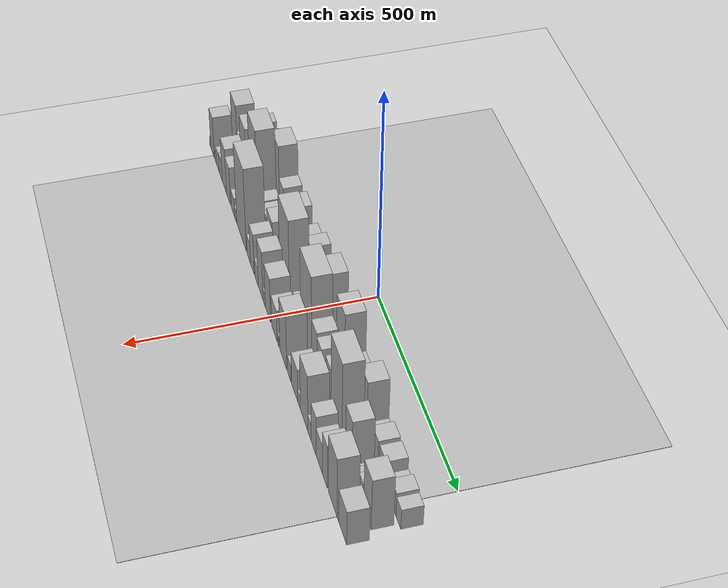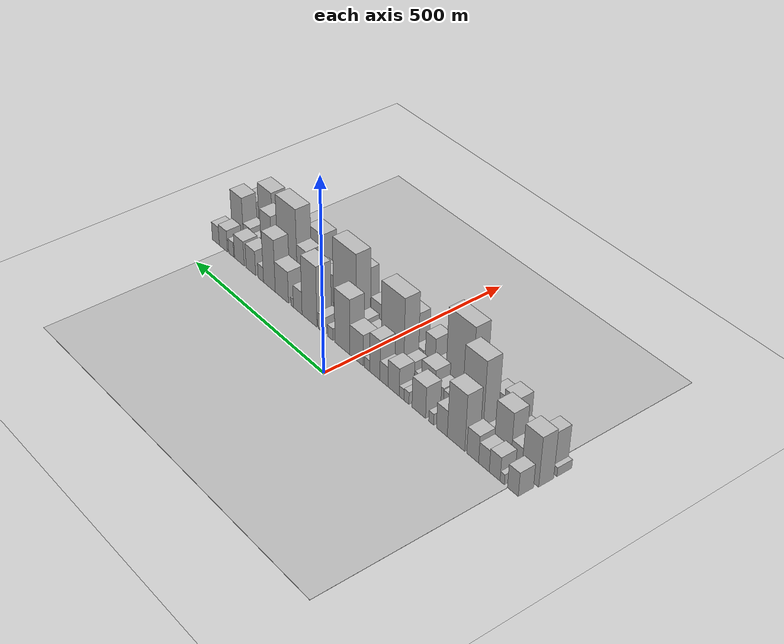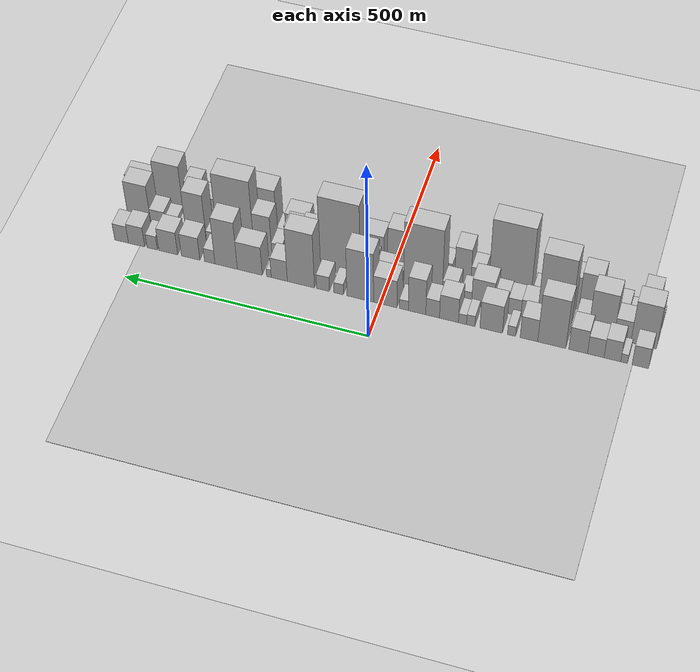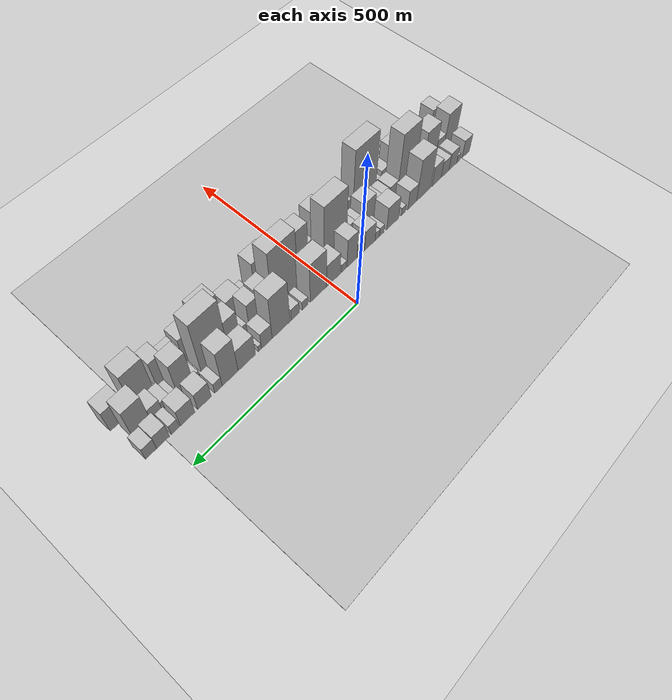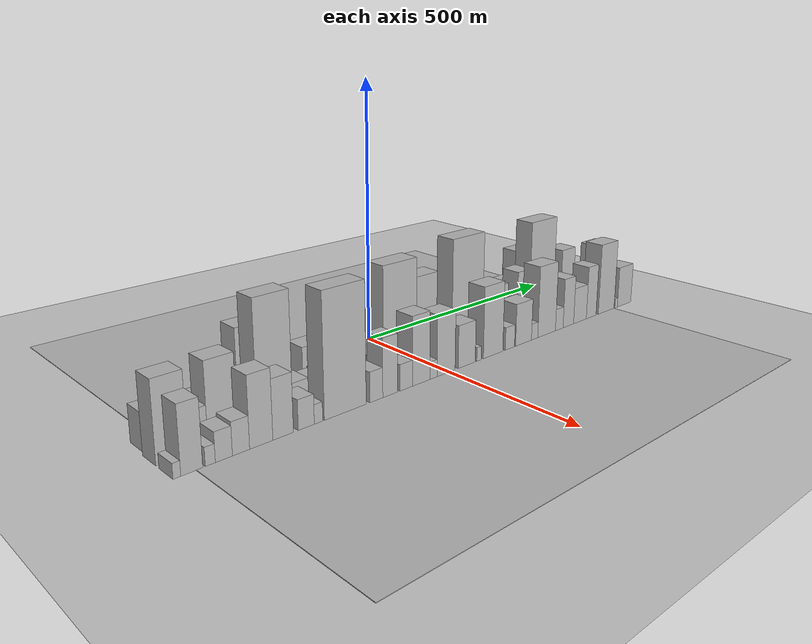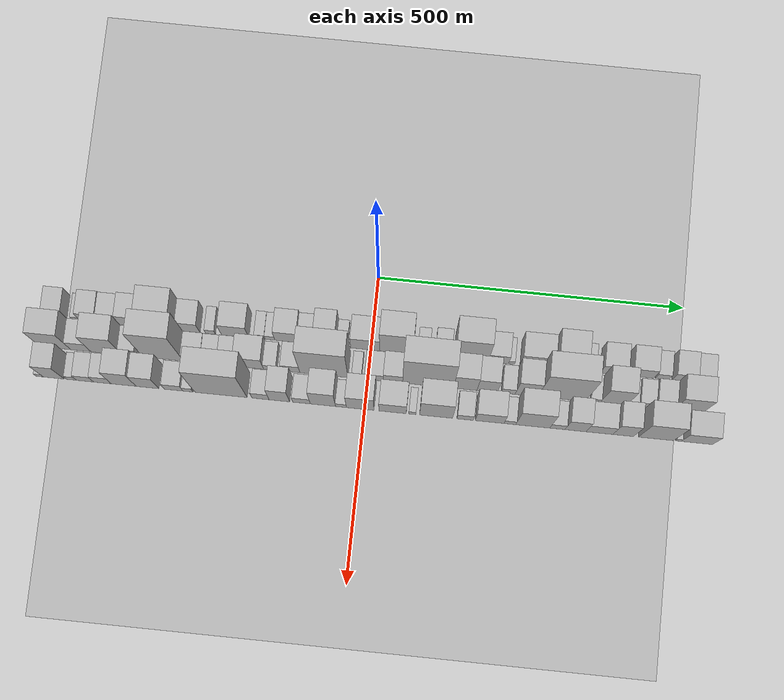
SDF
<?xml version="1.0" encoding="utf-8"?>

<sdf version="1.6">

   <world name="default">

      <gui fullscreen="0">

         <camera name="user_camera">

            <pose>-15 0 4.57585 0 0 0</pose>

            <view_controller>orbit</view_controller>

         </camera>

      </gui>

      <scene>

         <sky>

           <clouds>

             <speed>12</speed>

           </clouds>

         </sky>

         <ambient>0.4 0.4 0.4 1</ambient>

         <background>0.7 0.7 0.7 1</background>

         <shadows>1</shadows>

      </scene>

      <gravity>0 0 -9.8066</gravity>

      <magnetic_field>6e-06 2.3e-05 -4.2e-05</magnetic_field>

      <physics default="0" name="default_physics" type="ode">

         <ode>

            <solver>

               <type>quick</type>

               <iters>10</iters>

               <sor>1.0</sor>

               <use_dynamic_moi_rescaling>0</use_dynamic_moi_rescaling>

            </solver>

            <constraints>

               <cfm>0</cfm>

               <erp>0.2</erp>

               <contact_max_correcting_vel>100</contact_max_correcting_vel>

               <contact_surface_layer>0.001</contact_surface_layer>

            </constraints>

         </ode>

         <max_step_size>0.004</max_step_size>

         <real_time_factor>1</real_time_factor>

         <real_time_update_rate>250</real_time_update_rate>

      </physics>

      <light name="sun" type="directional">

         <cast_shadows>1</cast_shadows>

         <pose>0 0 10 0 0 0</pose>

         <diffuse>0.8 0.8 0.8 1</diffuse>

         <specular>0.2 0.2 0.2 1</specular>

         <attenuation>

            <range>1000</range>

            <constant>0.9</constant>

            <linear>0.01</linear>

            <quadratic>0.001</quadratic>

         </attenuation>

         <direction>-0.5 0.1 -0.9</direction>

      </light>

      <include>

         <name>ground_plane_1</name>

         <uri>model://HANNAS_ground_plane</uri>

         <pose>0 0 0  0 0 0</pose>

      </include>

      <include>

         <name>ground_plane_2</name>

         <uri>model://HANNAS_ground_plane</uri>

         <pose>100 0 0  0 0 0</pose>

      </include>

      <model name="building_1">

         <static>1</static>

         <pose frame="">100.0000 -515.0523 0 0.000000 0.000000 0.000000</pose>

         <link name="link">

            <pose frame="">0 0 31.50 0 0 0</pose>

            <collision name="collision">

               <geometry>

                  <box>

                     <size>40.0000 31.8954 63.0000</size>

                  </box>

               </geometry>

               <max_contacts>10</max_contacts>

               <surface>

                  <contact>

                     <ode/>

                  </contact>

                  <bounce/>

                  <friction>

                     <torsional>

                        <ode/>

                     </torsional>

                     <ode/>

                  </friction>

               </surface>

            </collision>

            <visual name="visual">

               <cast_shadows>0</cast_shadows>

               <geometry>

                  <box>

                     <size>40.0000 31.8954 63.0000</size>

                  </box>

               </geometry>

               <material>

                  <script>

                     <uri>model://HANNAS_wall/materials/scripts</uri>

                     <uri>model://HANNAS_wall/materials/textures</uri>

                     <name>vrc/HANNAS_wall</name>

                  </script>

               </material>

            </visual>

            <self_collide>0</self_collide>

            <enable_wind>0</enable_wind>

            <kinematic>0</kinematic>

         </link>

      </model>

      <model name="building_2">

         <static>1</static>

         <pose frame="">100.0000 -483.6169 0 0.000000 0.000000 0.000000</pose>

         <link name="link">

            <pose frame="">0 0 13.50 0 0 0</pose>

            <collision name="collision">

               <geometry>

                  <box>

                     <size>40.0000 12.9753 27.0000</size>

                  </box>

               </geometry>

               <max_contacts>10</max_contacts>

               <surface>

                  <contact>

                     <ode/>

                  </contact>

                  <bounce/>

                  <friction>

                     <torsional>

                        <ode/>

                     </torsional>

                     <ode/>

                  </friction>

               </surface>

            </collision>

            <visual name="visual">

               <cast_shadows>0</cast_shadows>

               <geometry>

                  <box>

                     <size>40.0000 12.9753 27.0000</size>

                  </box>

               </geometry>

               <material>

                  <script>

                     <uri>model://HANNAS_wall/materials/scripts</uri>

                     <uri>model://HANNAS_wall/materials/textures</uri>

                     <name>vrc/HANNAS_wall</name>

                  </script>

               </material>

            </visual>

            <self_collide>0</self_collide>

            <enable_wind>0</enable_wind>

            <kinematic>0</kinematic>

         </link>

      </model>

      <model name="building_3">

         <static>1</static>

         <pose frame="">100.0000 -460.8550 0 0.000000 0.000000 0.000000</pose>

         <link name="link">

            <pose frame="">0 0 31.50 0 0 0</pose>

            <collision name="collision">

               <geometry>

                  <box>

                     <size>40.0000 32.5485 63.0000</size>

                  </box>

               </geometry>

               <max_contacts>10</max_contacts>

               <surface>

                  <contact>

                     <ode/>

                  </contact>

                  <bounce/>

                  <friction>

                     <torsional>

                        <ode/>

                     </torsional>

                     <ode/>

                  </friction>

               </surface>

            </collision>

            <visual name="visual">

               <cast_shadows>0</cast_shadows>

               <geometry>

                  <box>

                     <size>40.0000 32.5485 63.0000</size>

                  </box>

               </geometry>

               <material>

                  <script>

                     <uri>model://HANNAS_wall/materials/scripts</uri>

                     <uri>model://HANNAS_wall/materials/textures</uri>

                     <name>vrc/HANNAS_wall</name>

                  </script>

               </material>

            </visual>

            <self_collide>0</self_collide>

            <enable_wind>0</enable_wind>

            <kinematic>0</kinematic>

         </link>

      </model>

      <model name="building_4">

         <static>1</static>

         <pose frame="">100.0000 -428.4344 0 0.000000 0.000000 0.000000</pose>

         <link name="link">

            <pose frame="">0 0 28.50 0 0 0</pose>

            <collision name="collision">

               <geometry>

                  <box>

                     <size>40.0000 32.2928 57.0000</size>

                  </box>

               </geometry>

               <max_contacts>10</max_contacts>

               <surface>

                  <contact>

                     <ode/>

                  </contact>

                  <bounce/>

                  <friction>

                     <torsional>

                        <ode/>

                     </torsional>

                     <ode/>

                  </friction>

               </surface>

            </collision>

            <visual name="visual">

               <cast_shadows>0</cast_shadows>

               <geometry>

                  <box>

                     <size>40.0000 32.2928 57.0000</size>

                  </box>

               </geometry>

               <material>

                  <script>

                     <uri>model://HANNAS_wall/materials/scripts</uri>

                     <uri>model://HANNAS_wall/materials/textures</uri>

                     <name>vrc/HANNAS_wall</name>

                  </script>

               </material>

            </visual>

            <self_collide>0</self_collide>

            <enable_wind>0</enable_wind>

            <kinematic>0</kinematic>

         </link>

      </model>

      <model name="building_5">

         <static>1</static>

         <pose frame="">100.0000 -394.0210 0 0.000000 0.000000 0.000000</pose>

         <link name="link">

            <pose frame="">0 0 36.00 0 0 0</pose>

            <collision name="collision">

               <geometry>

                  <box>

                     <size>40.0000 36.5340 72.0000</size>

                  </box>

               </geometry>

               <max_contacts>10</max_contacts>

               <surface>

                  <contact>

                     <ode/>

                  </contact>

                  <bounce/>

                  <friction>

                     <torsional>

                        <ode/>

                     </torsional>

                     <ode/>

                  </friction>

               </surface>

            </collision>

            <visual name="visual">

               <cast_shadows>0</cast_shadows>

               <geometry>

                  <box>

                     <size>40.0000 36.5340 72.0000</size>

                  </box>

               </geometry>

               <material>

                  <script>

                     <uri>model://HANNAS_wall/materials/scripts</uri>

                     <uri>model://HANNAS_wall/materials/textures</uri>

                     <name>vrc/HANNAS_wall</name>

                  </script>

               </material>

            </visual>

            <self_collide>0</self_collide>

            <enable_wind>0</enable_wind>

            <kinematic>0</kinematic>

         </link>

      </model>

      <model name="building_6">

         <static>1</static>

         <pose frame="">100.0000 -342.2416 0 0.000000 0.000000 0.000000</pose>

         <link name="link">

            <pose frame="">0 0 75.00 0 0 0</pose>

            <collision name="collision">

               <geometry>

                  <box>

                     <size>40.0000 55.0248 150.0000</size>

                  </box>

               </geometry>

               <max_contacts>10</max_contacts>

               <surface>

                  <contact>

                     <ode/>

                  </contact>

                  <bounce/>

                  <friction>

                     <torsional>

                        <ode/>

                     </torsional>

                     <ode/>

                  </friction>

               </surface>

            </collision>

            <visual name="visual">

               <cast_shadows>0</cast_shadows>

               <geometry>

                  <box>

                     <size>40.0000 55.0248 150.0000</size>

                  </box>

               </geometry>

               <material>

                  <script>

                     <uri>model://HANNAS_wall/materials/scripts</uri>

                     <uri>model://HANNAS_wall/materials/textures</uri>

                     <name>vrc/HANNAS_wall</name>

                  </script>

               </material>

            </visual>

            <self_collide>0</self_collide>

            <enable_wind>0</enable_wind>

            <kinematic>0</kinematic>

         </link>

      </model>

      <model name="building_7">

         <static>1</static>

         <pose frame="">100.0000 -297.3827 0 0.000000 0.000000 0.000000</pose>

         <link name="link">

            <pose frame="">0 0 34.50 0 0 0</pose>

            <collision name="collision">

               <geometry>

                  <box>

                     <size>40.0000 34.6930 69.0000</size>

                  </box>

               </geometry>

               <max_contacts>10</max_contacts>

               <surface>

                  <contact>

                     <ode/>

                  </contact>

                  <bounce/>

                  <friction>

                     <torsional>

                        <ode/>

                     </torsional>

                     <ode/>

                  </friction>

               </surface>

            </collision>

            <visual name="visual">

               <cast_shadows>0</cast_shadows>

               <geometry>

                  <box>

                     <size>40.0000 34.6930 69.0000</size>

                  </box>

               </geometry>

               <material>

                  <script>

                     <uri>model://HANNAS_wall/materials/scripts</uri>

                     <uri>model://HANNAS_wall/materials/textures</uri>

                     <name>vrc/HANNAS_wall</name>

                  </script>

               </material>

            </visual>

            <self_collide>0</self_collide>

            <enable_wind>0</enable_wind>

            <kinematic>0</kinematic>

         </link>

      </model>

      <model name="building_8">

         <static>1</static>

         <pose frame="">100.0000 -262.9456 0 0.000000 0.000000 0.000000</pose>

         <link name="link">

            <pose frame="">0 0 15.00 0 0 0</pose>

            <collision name="collision">

               <geometry>

                  <box>

                     <size>40.0000 16.1813 30.0000</size>

                  </box>

               </geometry>

               <max_contacts>10</max_contacts>

               <surface>

                  <contact>

                     <ode/>

                  </contact>

                  <bounce/>

                  <friction>

                     <torsional>

                        <ode/>

                     </torsional>

                     <ode/>

                  </friction>

               </surface>

            </collision>

            <visual name="visual">

               <cast_shadows>0</cast_shadows>

               <geometry>

                  <box>

                     <size>40.0000 16.1813 30.0000</size>

                  </box>

               </geometry>

               <material>

                  <script>

                     <uri>model://HANNAS_wall/materials/scripts</uri>

                     <uri>model://HANNAS_wall/materials/textures</uri>

                     <name>vrc/HANNAS_wall</name>

                  </script>

               </material>

            </visual>

            <self_collide>0</self_collide>

            <enable_wind>0</enable_wind>

            <kinematic>0</kinematic>

         </link>

      </model>

      <model name="building_9">

         <static>1</static>

         <pose frame="">100.0000 -222.4581 0 0.000000 0.000000 0.000000</pose>

         <link name="link">

            <pose frame="">0 0 42.00 0 0 0</pose>

            <collision name="collision">

               <geometry>

                  <box>

                     <size>40.0000 44.7938 84.0000</size>

                  </box>

               </geometry>

               <max_contacts>10</max_contacts>

               <surface>

                  <contact>

                     <ode/>

                  </contact>

                  <bounce/>

                  <friction>

                     <torsional>

                        <ode/>

                     </torsional>

                     <ode/>

                  </friction>

               </surface>

            </collision>

            <visual name="visual">

               <cast_shadows>0</cast_shadows>

               <geometry>

                  <box>

                     <size>40.0000 44.7938 84.0000</size>

                  </box>

               </geometry>

               <material>

                  <script>

                     <uri>model://HANNAS_wall/materials/scripts</uri>

                     <uri>model://HANNAS_wall/materials/textures</uri>

                     <name>vrc/HANNAS_wall</name>

                  </script>

               </material>

            </visual>

            <self_collide>0</self_collide>

            <enable_wind>0</enable_wind>

            <kinematic>0</kinematic>

         </link>

      </model>

      <model name="building_10">

         <static>1</static>

         <pose frame="">100.0000 -181.6860 0 0.000000 0.000000 0.000000</pose>

         <link name="link">

            <pose frame="">0 0 16.50 0 0 0</pose>

            <collision name="collision">

               <geometry>

                  <box>

                     <size>40.0000 16.7503 33.0000</size>

                  </box>

               </geometry>

               <max_contacts>10</max_contacts>

               <surface>

                  <contact>

                     <ode/>

                  </contact>

                  <bounce/>

                  <friction>

                     <torsional>

                        <ode/>

                     </torsional>

                     <ode/>

                  </friction>

               </surface>

            </collision>

            <visual name="visual">

               <cast_shadows>0</cast_shadows>

               <geometry>

                  <box>

                     <size>40.0000 16.7503 33.0000</size>

                  </box>

               </geometry>

               <material>

                  <script>

                     <uri>model://HANNAS_wall/materials/scripts</uri>

                     <uri>model://HANNAS_wall/materials/textures</uri>

                     <name>vrc/HANNAS_wall</name>

                  </script>

               </material>

            </visual>

            <self_collide>0</self_collide>

            <enable_wind>0</enable_wind>

            <kinematic>0</kinematic>

         </link>

      </model>

      <model name="building_11">

         <static>1</static>

         <pose frame="">100.0000 -165.3337 0 0.000000 0.000000 0.000000</pose>

         <link name="link">

            <pose frame="">0 0 15.00 0 0 0</pose>

            <collision name="collision">

               <geometry>

                  <box>

                     <size>40.0000 15.9544 30.0000</size>

                  </box>

               </geometry>

               <max_contacts>10</max_contacts>

               <surface>

                  <contact>

                     <ode/>

                  </contact>

                  <bounce/>

                  <friction>

                     <torsional>

                        <ode/>

                     </torsional>

                     <ode/>

                  </friction>

               </surface>

            </collision>

            <visual name="visual">

               <cast_shadows>0</cast_shadows>

               <geometry>

                  <box>

                     <size>40.0000 15.9544 30.0000</size>

                  </box>

               </geometry>

               <material>

                  <script>

                     <uri>model://HANNAS_wall/materials/scripts</uri>

                     <uri>model://HANNAS_wall/materials/textures</uri>

                     <name>vrc/HANNAS_wall</name>

                  </script>

               </material>

            </visual>

            <self_collide>0</self_collide>

            <enable_wind>0</enable_wind>

            <kinematic>0</kinematic>

         </link>

      </model>

      <model name="building_12">

         <static>1</static>

         <pose frame="">100.0000 -138.3691 0 0.000000 0.000000 0.000000</pose>

         <link name="link">

            <pose frame="">0 0 37.50 0 0 0</pose>

            <collision name="collision">

               <geometry>

                  <box>

                     <size>40.0000 37.9748 75.0000</size>

                  </box>

               </geometry>

               <max_contacts>10</max_contacts>

               <surface>

                  <contact>

                     <ode/>

                  </contact>

                  <bounce/>

                  <friction>

                     <torsional>

                        <ode/>

                     </torsional>

                     <ode/>

                  </friction>

               </surface>

            </collision>

            <visual name="visual">

               <cast_shadows>0</cast_shadows>

               <geometry>

                  <box>

                     <size>40.0000 37.9748 75.0000</size>

                  </box>

               </geometry>

               <material>

                  <script>

                     <uri>model://HANNAS_wall/materials/scripts</uri>

                     <uri>model://HANNAS_wall/materials/textures</uri>

                     <name>vrc/HANNAS_wall</name>

                  </script>

               </material>

            </visual>

            <self_collide>0</self_collide>

            <enable_wind>0</enable_wind>

            <kinematic>0</kinematic>

         </link>

      </model>

      <model name="building_13">

         <static>1</static>

         <pose frame="">100.0000 -105.5590 0 0.000000 0.000000 0.000000</pose>

         <link name="link">

            <pose frame="">0 0 27.00 0 0 0</pose>

            <collision name="collision">

               <geometry>

                  <box>

                     <size>40.0000 27.6454 54.0000</size>

                  </box>

               </geometry>

               <max_contacts>10</max_contacts>

               <surface>

                  <contact>

                     <ode/>

                  </contact>

                  <bounce/>

                  <friction>

                     <torsional>

                        <ode/>

                     </torsional>

                     <ode/>

                  </friction>

               </surface>

            </collision>

            <visual name="visual">

               <cast_shadows>0</cast_shadows>

               <geometry>

                  <box>

                     <size>40.0000 27.6454 54.0000</size>

                  </box>

               </geometry>

               <material>

                  <script>

                     <uri>model://HANNAS_wall/materials/scripts</uri>

                     <uri>model://HANNAS_wall/materials/textures</uri>

                     <name>vrc/HANNAS_wall</name>

                  </script>

               </material>

            </visual>

            <self_collide>0</self_collide>

            <enable_wind>0</enable_wind>

            <kinematic>0</kinematic>

         </link>

      </model>

      <model name="building_14">

         <static>1</static>

         <pose frame="">100.0000 -74.0861 0 0.000000 0.000000 0.000000</pose>

         <link name="link">

            <pose frame="">0 0 54.00 0 0 0</pose>

            <collision name="collision">

               <geometry>

                  <box>

                     <size>40.0000 35.3006 108.0000</size>

                  </box>

               </geometry>

               <max_contacts>10</max_contacts>

               <surface>

                  <contact>

                     <ode/>

                  </contact>

                  <bounce/>

                  <friction>

                     <torsional>

                        <ode/>

                     </torsional>

                     <ode/>

                  </friction>

               </surface>

            </collision>

            <visual name="visual">

               <cast_shadows>0</cast_shadows>

               <geometry>

                  <box>

                     <size>40.0000 35.3006 108.0000</size>

                  </box>

               </geometry>

               <material>

                  <script>

                     <uri>model://HANNAS_wall/materials/scripts</uri>

                     <uri>model://HANNAS_wall/materials/textures</uri>

                     <name>vrc/HANNAS_wall</name>

                  </script>

               </material>

            </visual>

            <self_collide>0</self_collide>

            <enable_wind>0</enable_wind>

            <kinematic>0</kinematic>

         </link>

      </model>

      <model name="building_15">

         <static>1</static>

         <pose frame="">100.0000 -47.4380 0 0.000000 0.000000 0.000000</pose>

         <link name="link">

            <pose frame="">0 0 15.00 0 0 0</pose>

            <collision name="collision">

               <geometry>

                  <box>

                     <size>40.0000 17.9956 30.0000</size>

                  </box>

               </geometry>

               <max_contacts>10</max_contacts>

               <surface>

                  <contact>

                     <ode/>

                  </contact>

                  <bounce/>

                  <friction>

                     <torsional>

                        <ode/>

                     </torsional>

                     <ode/>

                  </friction>

               </surface>

            </collision>

            <visual name="visual">

               <cast_shadows>0</cast_shadows>

               <geometry>

                  <box>

                     <size>40.0000 17.9956 30.0000</size>

                  </box>

               </geometry>

               <material>

                  <script>

                     <uri>model://HANNAS_wall/materials/scripts</uri>

                     <uri>model://HANNAS_wall/materials/textures</uri>

                     <name>vrc/HANNAS_wall</name>

                  </script>

               </material>

            </visual>

            <self_collide>0</self_collide>

            <enable_wind>0</enable_wind>

            <kinematic>0</kinematic>

         </link>

      </model>

      <model name="building_16">

         <static>1</static>

         <pose frame="">100.0000 -9.7221 0 0.000000 0.000000 0.000000</pose>

         <link name="link">

            <pose frame="">0 0 42.00 0 0 0</pose>

            <collision name="collision">

               <geometry>

                  <box>

                     <size>40.0000 47.4362 84.0000</size>

                  </box>

               </geometry>

               <max_contacts>10</max_contacts>

               <surface>

                  <contact>

                     <ode/>

                  </contact>

                  <bounce/>

                  <friction>

                     <torsional>

                        <ode/>

                     </torsional>

                     <ode/>

                  </friction>

               </surface>

            </collision>

            <visual name="visual">

               <cast_shadows>0</cast_shadows>

               <geometry>

                  <box>

                     <size>40.0000 47.4362 84.0000</size>

                  </box>

               </geometry>

               <material>

                  <script>

                     <uri>model://HANNAS_wall/materials/scripts</uri>

                     <uri>model://HANNAS_wall/materials/textures</uri>

                     <name>vrc/HANNAS_wall</name>

                  </script>

               </material>

            </visual>

            <self_collide>0</self_collide>

            <enable_wind>0</enable_wind>

            <kinematic>0</kinematic>

         </link>

      </model>

      <model name="building_17">

         <static>1</static>

         <pose frame="">100.0000 41.2047 0 0.000000 0.000000 0.000000</pose>

         <link name="link">

            <pose frame="">0 0 75.00 0 0 0</pose>

            <collision name="collision">

               <geometry>

                  <box>

                     <size>40.0000 54.4174 150.0000</size>

                  </box>

               </geometry>

               <max_contacts>10</max_contacts>

               <surface>

                  <contact>

                     <ode/>

                  </contact>

                  <bounce/>

                  <friction>

                     <torsional>

                        <ode/>

                     </torsional>

                     <ode/>

                  </friction>

               </surface>

            </collision>

            <visual name="visual">

               <cast_shadows>0</cast_shadows>

               <geometry>

                  <box>

                     <size>40.0000 54.4174 150.0000</size>

                  </box>

               </geometry>

               <material>

                  <script>

                     <uri>model://HANNAS_wall/materials/scripts</uri>

                     <uri>model://HANNAS_wall/materials/textures</uri>

                     <name>vrc/HANNAS_wall</name>

                  </script>

               </material>

            </visual>

            <self_collide>0</self_collide>

            <enable_wind>0</enable_wind>

            <kinematic>0</kinematic>

         </link>

      </model>

      <model name="building_18">

         <static>1</static>

         <pose frame="">100.0000 85.2992 0 0.000000 0.000000 0.000000</pose>

         <link name="link">

            <pose frame="">0 0 16.50 0 0 0</pose>

            <collision name="collision">

               <geometry>

                  <box>

                     <size>40.0000 19.7715 33.0000</size>

                  </box>

               </geometry>

               <max_contacts>10</max_contacts>

               <surface>

                  <contact>

                     <ode/>

                  </contact>

                  <bounce/>

                  <friction>

                     <torsional>

                        <ode/>

                     </torsional>

                     <ode/>

                  </friction>

               </surface>

            </collision>

            <visual name="visual">

               <cast_shadows>0</cast_shadows>

               <geometry>

                  <box>

                     <size>40.0000 19.7715 33.0000</size>

                  </box>

               </geometry>

               <material>

                  <script>

                     <uri>model://HANNAS_wall/materials/scripts</uri>

                     <uri>model://HANNAS_wall/materials/textures</uri>

                     <name>vrc/HANNAS_wall</name>

                  </script>

               </material>

            </visual>

            <self_collide>0</self_collide>

            <enable_wind>0</enable_wind>

            <kinematic>0</kinematic>

         </link>

      </model>

      <model name="building_19">

         <static>1</static>

         <pose frame="">100.0000 117.4299 0 0.000000 0.000000 0.000000</pose>

         <link name="link">

            <pose frame="">0 0 22.50 0 0 0</pose>

            <collision name="collision">

               <geometry>

                  <box>

                     <size>40.0000 26.4899 45.0000</size>

                  </box>

               </geometry>

               <max_contacts>10</max_contacts>

               <surface>

                  <contact>

                     <ode/>

                  </contact>

                  <bounce/>

                  <friction>

                     <torsional>

                        <ode/>

                     </torsional>

                     <ode/>

                  </friction>

               </surface>

            </collision>

            <visual name="visual">

               <cast_shadows>0</cast_shadows>

               <geometry>

                  <box>

                     <size>40.0000 26.4899 45.0000</size>

                  </box>

               </geometry>

               <material>

                  <script>

                     <uri>model://HANNAS_wall/materials/scripts</uri>

                     <uri>model://HANNAS_wall/materials/textures</uri>

                     <name>vrc/HANNAS_wall</name>

                  </script>

               </material>

            </visual>

            <self_collide>0</self_collide>

            <enable_wind>0</enable_wind>

            <kinematic>0</kinematic>

         </link>

      </model>

      <model name="building_20">

         <static>1</static>

         <pose frame="">100.0000 162.7504 0 0.000000 0.000000 0.000000</pose>

         <link name="link">

            <pose frame="">0 0 82.50 0 0 0</pose>

            <collision name="collision">

               <geometry>

                  <box>

                     <size>40.0000 56.1511 165.0000</size>

                  </box>

               </geometry>

               <max_contacts>10</max_contacts>

               <surface>

                  <contact>

                     <ode/>

                  </contact>

                  <bounce/>

                  <friction>

                     <torsional>

                        <ode/>

                     </torsional>

                     <ode/>

                  </friction>

               </surface>

            </collision>

            <visual name="visual">

               <cast_shadows>0</cast_shadows>

               <geometry>

                  <box>

                     <size>40.0000 56.1511 165.0000</size>

                  </box>

               </geometry>

               <material>

                  <script>

                     <uri>model://HANNAS_wall/materials/scripts</uri>

                     <uri>model://HANNAS_wall/materials/textures</uri>

                     <name>vrc/HANNAS_wall</name>

                  </script>

               </material>

            </visual>

            <self_collide>0</self_collide>

            <enable_wind>0</enable_wind>

            <kinematic>0</kinematic>

         </link>

      </model>

      <model name="building_21">

         <static>1</static>

         <pose frame="">100.0000 207.4724 0 0.000000 0.000000 0.000000</pose>

         <link name="link">

            <pose frame="">0 0 31.50 0 0 0</pose>

            <collision name="collision">

               <geometry>

                  <box>

                     <size>40.0000 33.2930 63.0000</size>

                  </box>

               </geometry>

               <max_contacts>10</max_contacts>

               <surface>

                  <contact>

                     <ode/>

                  </contact>

                  <bounce/>

                  <friction>

                     <torsional>

                        <ode/>

                     </torsional>

                     <ode/>

                  </friction>

               </surface>

            </collision>

            <visual name="visual">

               <cast_shadows>0</cast_shadows>

               <geometry>

                  <box>

                     <size>40.0000 33.2930 63.0000</size>

                  </box>

               </geometry>

               <material>

                  <script>

                     <uri>model://HANNAS_wall/materials/scripts</uri>

                     <uri>model://HANNAS_wall/materials/textures</uri>

                     <name>vrc/HANNAS_wall</name>

                  </script>

               </material>

            </visual>

            <self_collide>0</self_collide>

            <enable_wind>0</enable_wind>

            <kinematic>0</kinematic>

         </link>

      </model>

      <model name="building_22">

         <static>1</static>

         <pose frame="">100.0000 228.9524 0 0.000000 0.000000 0.000000</pose>

         <link name="link">

            <pose frame="">0 0 12.00 0 0 0</pose>

            <collision name="collision">

               <geometry>

                  <box>

                     <size>40.0000 9.6670 24.0000</size>

                  </box>

               </geometry>

               <max_contacts>10</max_contacts>

               <surface>

                  <contact>

                     <ode/>

                  </contact>

                  <bounce/>

                  <friction>

                     <torsional>

                        <ode/>

                     </torsional>

                     <ode/>

                  </friction>

               </surface>

            </collision>

            <visual name="visual">

               <cast_shadows>0</cast_shadows>

               <geometry>

                  <box>

                     <size>40.0000 9.6670 24.0000</size>

                  </box>

               </geometry>

               <material>

                  <script>

                     <uri>model://HANNAS_wall/materials/scripts</uri>

                     <uri>model://HANNAS_wall/materials/textures</uri>

                     <name>vrc/HANNAS_wall</name>

                  </script>

               </material>

            </visual>

            <self_collide>0</self_collide>

            <enable_wind>0</enable_wind>

            <kinematic>0</kinematic>

         </link>

      </model>

      <model name="building_23">

         <static>1</static>

         <pose frame="">100.0000 268.7100 0 0.000000 0.000000 0.000000</pose>

         <link name="link">

            <pose frame="">0 0 43.50 0 0 0</pose>

            <collision name="collision">

               <geometry>

                  <box>

                     <size>40.0000 51.8483 87.0000</size>

                  </box>

               </geometry>

               <max_contacts>10</max_contacts>

               <surface>

                  <contact>

                     <ode/>

                  </contact>

                  <bounce/>

                  <friction>

                     <torsional>

                        <ode/>

                     </torsional>

                     <ode/>

                  </friction>

               </surface>

            </collision>

            <visual name="visual">

               <cast_shadows>0</cast_shadows>

               <geometry>

                  <box>

                     <size>40.0000 51.8483 87.0000</size>

                  </box>

               </geometry>

               <material>

                  <script>

                     <uri>model://HANNAS_wall/materials/scripts</uri>

                     <uri>model://HANNAS_wall/materials/textures</uri>

                     <name>vrc/HANNAS_wall</name>

                  </script>

               </material>

            </visual>

            <self_collide>0</self_collide>

            <enable_wind>0</enable_wind>

            <kinematic>0</kinematic>

         </link>

      </model>

      <model name="building_24">

         <static>1</static>

         <pose frame="">100.0000 318.0500 0 0.000000 0.000000 0.000000</pose>

         <link name="link">

            <pose frame="">0 0 72.00 0 0 0</pose>

            <collision name="collision">

               <geometry>

                  <box>

                     <size>40.0000 46.8317 144.0000</size>

                  </box>

               </geometry>

               <max_contacts>10</max_contacts>

               <surface>

                  <contact>

                     <ode/>

                  </contact>

                  <bounce/>

                  <friction>

                     <torsional>

                        <ode/>

                     </torsional>

                     <ode/>

                  </friction>

               </surface>

            </collision>

            <visual name="visual">

               <cast_shadows>0</cast_shadows>

               <geometry>

                  <box>

                     <size>40.0000 46.8317 144.0000</size>

                  </box>

               </geometry>

               <material>

                  <script>

                     <uri>model://HANNAS_wall/materials/scripts</uri>

                     <uri>model://HANNAS_wall/materials/textures</uri>

                     <name>vrc/HANNAS_wall</name>

                  </script>

               </material>

            </visual>

            <self_collide>0</self_collide>

            <enable_wind>0</enable_wind>

            <kinematic>0</kinematic>

         </link>

      </model>

      <model name="building_25">

         <static>1</static>

         <pose frame="">100.0000 352.3930 0 0.000000 0.000000 0.000000</pose>

         <link name="link">

            <pose frame="">0 0 21.00 0 0 0</pose>

            <collision name="collision">

               <geometry>

                  <box>

                     <size>40.0000 21.8542 42.0000</size>

                  </box>

               </geometry>

               <max_contacts>10</max_contacts>

               <surface>

                  <contact>

                     <ode/>

                  </contact>

                  <bounce/>

                  <friction>

                     <torsional>

                        <ode/>

                     </torsional>

                     <ode/>

                  </friction>

               </surface>

            </collision>

            <visual name="visual">

               <cast_shadows>0</cast_shadows>

               <geometry>

                  <box>

                     <size>40.0000 21.8542 42.0000</size>

                  </box>

               </geometry>

               <material>

                  <script>

                     <uri>model://HANNAS_wall/materials/scripts</uri>

                     <uri>model://HANNAS_wall/materials/textures</uri>

                     <name>vrc/HANNAS_wall</name>

                  </script>

               </material>

            </visual>

            <self_collide>0</self_collide>

            <enable_wind>0</enable_wind>

            <kinematic>0</kinematic>

         </link>

      </model>

      <model name="building_26">

         <static>1</static>

         <pose frame="">100.0000 392.6791 0 0.000000 0.000000 0.000000</pose>

         <link name="link">

            <pose frame="">0 0 34.50 0 0 0</pose>

            <collision name="collision">

               <geometry>

                  <box>

                     <size>40.0000 38.7181 69.0000</size>

                  </box>

               </geometry>

               <max_contacts>10</max_contacts>

               <surface>

                  <contact>

                     <ode/>

                  </contact>

                  <bounce/>

                  <friction>

                     <torsional>

                        <ode/>

                     </torsional>

                     <ode/>

                  </friction>

               </surface>

            </collision>

            <visual name="visual">

               <cast_shadows>0</cast_shadows>

               <geometry>

                  <box>

                     <size>40.0000 38.7181 69.0000</size>

                  </box>

               </geometry>

               <material>

                  <script>

                     <uri>model://HANNAS_wall/materials/scripts</uri>

                     <uri>model://HANNAS_wall/materials/textures</uri>

                     <name>vrc/HANNAS_wall</name>

                  </script>

               </material>

            </visual>

            <self_collide>0</self_collide>

            <enable_wind>0</enable_wind>

            <kinematic>0</kinematic>

         </link>

      </model>

      <model name="building_27">

         <static>1</static>

         <pose frame="">100.0000 440.0638 0 0.000000 0.000000 0.000000</pose>

         <link name="link">

            <pose frame="">0 0 34.50 0 0 0</pose>

            <collision name="collision">

               <geometry>

                  <box>

                     <size>40.0000 40.0512 69.0000</size>

                  </box>

               </geometry>

               <max_contacts>10</max_contacts>

               <surface>

                  <contact>

                     <ode/>

                  </contact>

                  <bounce/>

                  <friction>

                     <torsional>

                        <ode/>

                     </torsional>

                     <ode/>

                  </friction>

               </surface>

            </collision>

            <visual name="visual">

               <cast_shadows>0</cast_shadows>

               <geometry>

                  <box>

                     <size>40.0000 40.0512 69.0000</size>

                  </box>

               </geometry>

               <material>

                  <script>

                     <uri>model://HANNAS_wall/materials/scripts</uri>

                     <uri>model://HANNAS_wall/materials/textures</uri>

                     <name>vrc/HANNAS_wall</name>

                  </script>

               </material>

            </visual>

            <self_collide>0</self_collide>

            <enable_wind>0</enable_wind>

            <kinematic>0</kinematic>

         </link>

      </model>

      <model name="building_28">

         <static>1</static>

         <pose frame="">100.0000 473.9851 0 0.000000 0.000000 0.000000</pose>

         <link name="link">

            <pose frame="">0 0 21.00 0 0 0</pose>

            <collision name="collision">

               <geometry>

                  <box>

                     <size>40.0000 21.7914 42.0000</size>

                  </box>

               </geometry>

               <max_contacts>10</max_contacts>

               <surface>

                  <contact>

                     <ode/>

                  </contact>

                  <bounce/>

                  <friction>

                     <torsional>

                        <ode/>

                     </torsional>

                     <ode/>

                  </friction>

               </surface>

            </collision>

            <visual name="visual">

               <cast_shadows>0</cast_shadows>

               <geometry>

                  <box>

                     <size>40.0000 21.7914 42.0000</size>

                  </box>

               </geometry>

               <material>

                  <script>

                     <uri>model://HANNAS_wall/materials/scripts</uri>

                     <uri>model://HANNAS_wall/materials/textures</uri>

                     <name>vrc/HANNAS_wall</name>

                  </script>

               </material>

            </visual>

            <self_collide>0</self_collide>

            <enable_wind>0</enable_wind>

            <kinematic>0</kinematic>

         </link>

      </model>

      <model name="building_29">

         <static>1</static>

         <pose frame="">100.0000 507.1478 0 0.000000 0.000000 0.000000</pose>

         <link name="link">

            <pose frame="">0 0 30.00 0 0 0</pose>

            <collision name="collision">

               <geometry>

                  <box>

                     <size>40.0000 34.5340 60.0000</size>

                  </box>

               </geometry>

               <max_contacts>10</max_contacts>

               <surface>

                  <contact>

                     <ode/>

                  </contact>

                  <bounce/>

                  <friction>

                     <torsional>

                        <ode/>

                     </torsional>

                     <ode/>

                  </friction>

               </surface>

            </collision>

            <visual name="visual">

               <cast_shadows>0</cast_shadows>

               <geometry>

                  <box>

                     <size>40.0000 34.5340 60.0000</size>

                  </box>

               </geometry>

               <material>

                  <script>

                     <uri>model://HANNAS_wall/materials/scripts</uri>

                     <uri>model://HANNAS_wall/materials/textures</uri>

                     <name>vrc/HANNAS_wall</name>

                  </script>

               </material>

            </visual>

            <self_collide>0</self_collide>

            <enable_wind>0</enable_wind>

            <kinematic>0</kinematic>

         </link>

      </model>

      <model name="building_30">

         <static>1</static>

         <pose frame="">100.0000 539.1246 0 0.000000 0.000000 0.000000</pose>

         <link name="link">

            <pose frame="">0 0 25.50 0 0 0</pose>

            <collision name="collision">

               <geometry>

                  <box>

                     <size>40.0000 29.4196 51.0000</size>

                  </box>

               </geometry>

               <max_contacts>10</max_contacts>

               <surface>

                  <contact>

                     <ode/>

                  </contact>

                  <bounce/>

                  <friction>

                     <torsional>

                        <ode/>

                     </torsional>

                     <ode/>

                  </friction>

               </surface>

            </collision>

            <visual name="visual">

               <cast_shadows>0</cast_shadows>

               <geometry>

                  <box>

                     <size>40.0000 29.4196 51.0000</size>

                  </box>

               </geometry>

               <material>

                  <script>

                     <uri>model://HANNAS_wall/materials/scripts</uri>

                     <uri>model://HANNAS_wall/materials/textures</uri>

                     <name>vrc/HANNAS_wall</name>

                  </script>

               </material>

            </visual>

            <self_collide>0</self_collide>

            <enable_wind>0</enable_wind>

            <kinematic>0</kinematic>

         </link>

      </model>

      <model name="building_31">

         <static>1</static>

         <pose frame="">149.0000 -510.9275 0 0.000000 0.000000 0.000000</pose>

         <link name="link">

            <pose frame="">0 0 66.00 0 0 0</pose>

            <collision name="collision">

               <geometry>

                  <box>

                     <size>40.0000 50.1451 132.0000</size>

                  </box>

               </geometry>

               <max_contacts>10</max_contacts>

               <surface>

                  <contact>

                     <ode/>

                  </contact>

                  <bounce/>

                  <friction>

                     <torsional>

                        <ode/>

                     </torsional>

                     <ode/>

                  </friction>

               </surface>

            </collision>

            <visual name="visual">

               <cast_shadows>0</cast_shadows>

               <geometry>

                  <box>

                     <size>40.0000 50.1451 132.0000</size>

                  </box>

               </geometry>

               <material>

                  <script>

                     <uri>model://HANNAS_wall/materials/scripts</uri>

                     <uri>model://HANNAS_wall/materials/textures</uri>

                     <name>vrc/HANNAS_wall</name>

                  </script>

               </material>

            </visual>

            <self_collide>0</self_collide>

            <enable_wind>0</enable_wind>

            <kinematic>0</kinematic>

         </link>

      </model>

      <model name="building_32">

         <static>1</static>

         <pose frame="">149.0000 -469.3232 0 0.000000 0.000000 0.000000</pose>

         <link name="link">

            <pose frame="">0 0 33.00 0 0 0</pose>

            <collision name="collision">

               <geometry>

                  <box>

                     <size>40.0000 33.0634 66.0000</size>

                  </box>

               </geometry>

               <max_contacts>10</max_contacts>

               <surface>

                  <contact>

                     <ode/>

                  </contact>

                  <bounce/>

                  <friction>

                     <torsional>

                        <ode/>

                     </torsional>

                     <ode/>

                  </friction>

               </surface>

            </collision>

            <visual name="visual">

               <cast_shadows>0</cast_shadows>

               <geometry>

                  <box>

                     <size>40.0000 33.0634 66.0000</size>

                  </box>

               </geometry>

               <material>

                  <script>

                     <uri>model://HANNAS_wall/materials/scripts</uri>

                     <uri>model://HANNAS_wall/materials/textures</uri>

                     <name>vrc/HANNAS_wall</name>

                  </script>

               </material>

            </visual>

            <self_collide>0</self_collide>

            <enable_wind>0</enable_wind>

            <kinematic>0</kinematic>

         </link>

      </model>

      <model name="building_33">

         <static>1</static>

         <pose frame="">149.0000 -427.5966 0 0.000000 0.000000 0.000000</pose>

         <link name="link">

            <pose frame="">0 0 67.50 0 0 0</pose>

            <collision name="collision">

               <geometry>

                  <box>

                     <size>40.0000 50.3898 135.0000</size>

                  </box>

               </geometry>

               <max_contacts>10</max_contacts>

               <surface>

                  <contact>

                     <ode/>

                  </contact>

                  <bounce/>

                  <friction>

                     <torsional>

                        <ode/>

                     </torsional>

                     <ode/>

                  </friction>

               </surface>

            </collision>

            <visual name="visual">

               <cast_shadows>0</cast_shadows>

               <geometry>

                  <box>

                     <size>40.0000 50.3898 135.0000</size>

                  </box>

               </geometry>

               <material>

                  <script>

                     <uri>model://HANNAS_wall/materials/scripts</uri>

                     <uri>model://HANNAS_wall/materials/textures</uri>

                     <name>vrc/HANNAS_wall</name>

                  </script>

               </material>

            </visual>

            <self_collide>0</self_collide>

            <enable_wind>0</enable_wind>

            <kinematic>0</kinematic>

         </link>

      </model>

      <model name="building_34">

         <static>1</static>

         <pose frame="">149.0000 -388.8592 0 0.000000 0.000000 0.000000</pose>

         <link name="link">

            <pose frame="">0 0 25.50 0 0 0</pose>

            <collision name="collision">

               <geometry>

                  <box>

                     <size>40.0000 27.0851 51.0000</size>

                  </box>

               </geometry>

               <max_contacts>10</max_contacts>

               <surface>

                  <contact>

                     <ode/>

                  </contact>

                  <bounce/>

                  <friction>

                     <torsional>

                        <ode/>

                     </torsional>

                     <ode/>

                  </friction>

               </surface>

            </collision>

            <visual name="visual">

               <cast_shadows>0</cast_shadows>

               <geometry>

                  <box>

                     <size>40.0000 27.0851 51.0000</size>

                  </box>

               </geometry>

               <material>

                  <script>

                     <uri>model://HANNAS_wall/materials/scripts</uri>

                     <uri>model://HANNAS_wall/materials/textures</uri>

                     <name>vrc/HANNAS_wall</name>

                  </script>

               </material>

            </visual>

            <self_collide>0</self_collide>

            <enable_wind>0</enable_wind>

            <kinematic>0</kinematic>

         </link>

      </model>

      <model name="building_35">

         <static>1</static>

         <pose frame="">149.0000 -334.2735 0 0.000000 0.000000 0.000000</pose>

         <link name="link">

            <pose frame="">0 0 105.00 0 0 0</pose>

            <collision name="collision">

               <geometry>

                  <box>

                     <size>40.0000 66.0862 210.0000</size>

                  </box>

               </geometry>

               <max_contacts>10</max_contacts>

               <surface>

                  <contact>

                     <ode/>

                  </contact>

                  <bounce/>

                  <friction>

                     <torsional>

                        <ode/>

                     </torsional>

                     <ode/>

                  </friction>

               </surface>

            </collision>

            <visual name="visual">

               <cast_shadows>0</cast_shadows>

               <geometry>

                  <box>

                     <size>40.0000 66.0862 210.0000</size>

                  </box>

               </geometry>

               <material>

                  <script>

                     <uri>model://HANNAS_wall/materials/scripts</uri>

                     <uri>model://HANNAS_wall/materials/textures</uri>

                     <name>vrc/HANNAS_wall</name>

                  </script>

               </material>

            </visual>

            <self_collide>0</self_collide>

            <enable_wind>0</enable_wind>

            <kinematic>0</kinematic>

         </link>

      </model>

      <model name="building_36">

         <static>1</static>

         <pose frame="">149.0000 -285.1975 0 0.000000 0.000000 0.000000</pose>

         <link name="link">

            <pose frame="">0 0 27.00 0 0 0</pose>

            <collision name="collision">

               <geometry>

                  <box>

                     <size>40.0000 32.0659 54.0000</size>

                  </box>

               </geometry>

               <max_contacts>10</max_contacts>

               <surface>

                  <contact>

                     <ode/>

                  </contact>

                  <bounce/>

                  <friction>

                     <torsional>

                        <ode/>

                     </torsional>

                     <ode/>

                  </friction>

               </surface>

            </collision>

            <visual name="visual">

               <cast_shadows>0</cast_shadows>

               <geometry>

                  <box>

                     <size>40.0000 32.0659 54.0000</size>

                  </box>

               </geometry>

               <material>

                  <script>

                     <uri>model://HANNAS_wall/materials/scripts</uri>

                     <uri>model://HANNAS_wall/materials/textures</uri>

                     <name>vrc/HANNAS_wall</name>

                  </script>

               </material>

            </visual>

            <self_collide>0</self_collide>

            <enable_wind>0</enable_wind>

            <kinematic>0</kinematic>

         </link>

      </model>

      <model name="building_37">

         <static>1</static>

         <pose frame="">149.0000 -255.9622 0 0.000000 0.000000 0.000000</pose>

         <link name="link">

            <pose frame="">0 0 25.50 0 0 0</pose>

            <collision name="collision">

               <geometry>

                  <box>

                     <size>40.0000 26.4046 51.0000</size>

                  </box>

               </geometry>

               <max_contacts>10</max_contacts>

               <surface>

                  <contact>

                     <ode/>

                  </contact>

                  <bounce/>

                  <friction>

                     <torsional>

                        <ode/>

                     </torsional>

                     <ode/>

                  </friction>

               </surface>

            </collision>

            <visual name="visual">

               <cast_shadows>0</cast_shadows>

               <geometry>

                  <box>

                     <size>40.0000 26.4046 51.0000</size>

                  </box>

               </geometry>

               <material>

                  <script>

                     <uri>model://HANNAS_wall/materials/scripts</uri>

                     <uri>model://HANNAS_wall/materials/textures</uri>

                     <name>vrc/HANNAS_wall</name>

                  </script>

               </material>

            </visual>

            <self_collide>0</self_collide>

            <enable_wind>0</enable_wind>

            <kinematic>0</kinematic>

         </link>

      </model>

      <model name="building_38">

         <static>1</static>

         <pose frame="">149.0000 -228.9502 0 0.000000 0.000000 0.000000</pose>

         <link name="link">

            <pose frame="">0 0 27.00 0 0 0</pose>

            <collision name="collision">

               <geometry>

                  <box>

                     <size>40.0000 27.6195 54.0000</size>

                  </box>

               </geometry>

               <max_contacts>10</max_contacts>

               <surface>

                  <contact>

                     <ode/>

                  </contact>

                  <bounce/>

                  <friction>

                     <torsional>

                        <ode/>

                     </torsional>

                     <ode/>

                  </friction>

               </surface>

            </collision>

            <visual name="visual">

               <cast_shadows>0</cast_shadows>

               <geometry>

                  <box>

                     <size>40.0000 27.6195 54.0000</size>

                  </box>

               </geometry>

               <material>

                  <script>

                     <uri>model://HANNAS_wall/materials/scripts</uri>

                     <uri>model://HANNAS_wall/materials/textures</uri>

                     <name>vrc/HANNAS_wall</name>

                  </script>

               </material>

            </visual>

            <self_collide>0</self_collide>

            <enable_wind>0</enable_wind>

            <kinematic>0</kinematic>

         </link>

      </model>

      <model name="building_39">

         <static>1</static>

         <pose frame="">149.0000 -192.6063 0 0.000000 0.000000 0.000000</pose>

         <link name="link">

            <pose frame="">0 0 42.00 0 0 0</pose>

            <collision name="collision">

               <geometry>

                  <box>

                     <size>40.0000 45.0681 84.0000</size>

                  </box>

               </geometry>

               <max_contacts>10</max_contacts>

               <surface>

                  <contact>

                     <ode/>

                  </contact>

                  <bounce/>

                  <friction>

                     <torsional>

                        <ode/>

                     </torsional>

                     <ode/>

                  </friction>

               </surface>

            </collision>

            <visual name="visual">

               <cast_shadows>0</cast_shadows>

               <geometry>

                  <box>

                     <size>40.0000 45.0681 84.0000</size>

                  </box>

               </geometry>

               <material>

                  <script>

                     <uri>model://HANNAS_wall/materials/scripts</uri>

                     <uri>model://HANNAS_wall/materials/textures</uri>

                     <name>vrc/HANNAS_wall</name>

                  </script>

               </material>

            </visual>

            <self_collide>0</self_collide>

            <enable_wind>0</enable_wind>

            <kinematic>0</kinematic>

         </link>

      </model>

      <model name="building_40">

         <static>1</static>

         <pose frame="">149.0000 -159.1830 0 0.000000 0.000000 0.000000</pose>

         <link name="link">

            <pose frame="">0 0 19.50 0 0 0</pose>

            <collision name="collision">

               <geometry>

                  <box>

                     <size>40.0000 21.7786 39.0000</size>

                  </box>

               </geometry>

               <max_contacts>10</max_contacts>

               <surface>

                  <contact>

                     <ode/>

                  </contact>

                  <bounce/>

                  <friction>

                     <torsional>

                        <ode/>

                     </torsional>

                     <ode/>

                  </friction>

               </surface>

            </collision>

            <visual name="visual">

               <cast_shadows>0</cast_shadows>

               <geometry>

                  <box>

                     <size>40.0000 21.7786 39.0000</size>

                  </box>

               </geometry>

               <material>

                  <script>

                     <uri>model://HANNAS_wall/materials/scripts</uri>

                     <uri>model://HANNAS_wall/materials/textures</uri>

                     <name>vrc/HANNAS_wall</name>

                  </script>

               </material>

            </visual>

            <self_collide>0</self_collide>

            <enable_wind>0</enable_wind>

            <kinematic>0</kinematic>

         </link>

      </model>

      <model name="building_41">

         <static>1</static>

         <pose frame="">149.0000 -126.1168 0 0.000000 0.000000 0.000000</pose>

         <link name="link">

            <pose frame="">0 0 27.00 0 0 0</pose>

            <collision name="collision">

               <geometry>

                  <box>

                     <size>40.0000 30.3538 54.0000</size>

                  </box>

               </geometry>

               <max_contacts>10</max_contacts>

               <surface>

                  <contact>

                     <ode/>

                  </contact>

                  <bounce/>

                  <friction>

                     <torsional>

                        <ode/>

                     </torsional>

                     <ode/>

                  </friction>

               </surface>

            </collision>

            <visual name="visual">

               <cast_shadows>0</cast_shadows>

               <geometry>

                  <box>

                     <size>40.0000 30.3538 54.0000</size>

                  </box>

               </geometry>

               <material>

                  <script>

                     <uri>model://HANNAS_wall/materials/scripts</uri>

                     <uri>model://HANNAS_wall/materials/textures</uri>

                     <name>vrc/HANNAS_wall</name>

                  </script>

               </material>

            </visual>

            <self_collide>0</self_collide>

            <enable_wind>0</enable_wind>

            <kinematic>0</kinematic>

         </link>

      </model>

      <model name="building_42">

         <static>1</static>

         <pose frame="">149.0000 -71.7669 0 0.000000 0.000000 0.000000</pose>

         <link name="link">

            <pose frame="">0 0 103.50 0 0 0</pose>

            <collision name="collision">

               <geometry>

                  <box>

                     <size>40.0000 78.3459 207.0000</size>

                  </box>

               </geometry>

               <max_contacts>10</max_contacts>

               <surface>

                  <contact>

                     <ode/>

                  </contact>

                  <bounce/>

                  <friction>

                     <torsional>

                        <ode/>

                     </torsional>

                     <ode/>

                  </friction>

               </surface>

            </collision>

            <visual name="visual">

               <cast_shadows>0</cast_shadows>

               <geometry>

                  <box>

                     <size>40.0000 78.3459 207.0000</size>

                  </box>

               </geometry>

               <material>

                  <script>

                     <uri>model://HANNAS_wall/materials/scripts</uri>

                     <uri>model://HANNAS_wall/materials/textures</uri>

                     <name>vrc/HANNAS_wall</name>

                  </script>

               </material>

            </visual>

            <self_collide>0</self_collide>

            <enable_wind>0</enable_wind>

            <kinematic>0</kinematic>

         </link>

      </model>

      <model name="building_43">

         <static>1</static>

         <pose frame="">149.0000 -18.5500 0 0.000000 0.000000 0.000000</pose>

         <link name="link">

            <pose frame="">0 0 15.00 0 0 0</pose>

            <collision name="collision">

               <geometry>

                  <box>

                     <size>40.0000 16.0880 30.0000</size>

                  </box>

               </geometry>

               <max_contacts>10</max_contacts>

               <surface>

                  <contact>

                     <ode/>

                  </contact>

                  <bounce/>

                  <friction>

                     <torsional>

                        <ode/>

                     </torsional>

                     <ode/>

                  </friction>

               </surface>

            </collision>

            <visual name="visual">

               <cast_shadows>0</cast_shadows>

               <geometry>

                  <box>

                     <size>40.0000 16.0880 30.0000</size>

                  </box>

               </geometry>

               <material>

                  <script>

                     <uri>model://HANNAS_wall/materials/scripts</uri>

                     <uri>model://HANNAS_wall/materials/textures</uri>

                     <name>vrc/HANNAS_wall</name>

                  </script>

               </material>

            </visual>

            <self_collide>0</self_collide>

            <enable_wind>0</enable_wind>

            <kinematic>0</kinematic>

         </link>

      </model>

      <model name="building_44">

         <static>1</static>

         <pose frame="">149.0000 9.5778 0 0.000000 0.000000 0.000000</pose>

         <link name="link">

            <pose frame="">0 0 25.50 0 0 0</pose>

            <collision name="collision">

               <geometry>

                  <box>

                     <size>40.0000 30.1677 51.0000</size>

                  </box>

               </geometry>

               <max_contacts>10</max_contacts>

               <surface>

                  <contact>

                     <ode/>

                  </contact>

                  <bounce/>

                  <friction>

                     <torsional>

                        <ode/>

                     </torsional>

                     <ode/>

                  </friction>

               </surface>

            </collision>

            <visual name="visual">

               <cast_shadows>0</cast_shadows>

               <geometry>

                  <box>

                     <size>40.0000 30.1677 51.0000</size>

                  </box>

               </geometry>

               <material>

                  <script>

                     <uri>model://HANNAS_wall/materials/scripts</uri>

                     <uri>model://HANNAS_wall/materials/textures</uri>

                     <name>vrc/HANNAS_wall</name>

                  </script>

               </material>

            </visual>

            <self_collide>0</self_collide>

            <enable_wind>0</enable_wind>

            <kinematic>0</kinematic>

         </link>

      </model>

      <model name="building_45">

         <static>1</static>

         <pose frame="">149.0000 40.5013 0 0.000000 0.000000 0.000000</pose>

         <link name="link">

            <pose frame="">0 0 31.50 0 0 0</pose>

            <collision name="collision">

               <geometry>

                  <box>

                     <size>40.0000 31.6792 63.0000</size>

                  </box>

               </geometry>

               <max_contacts>10</max_contacts>

               <surface>

                  <contact>

                     <ode/>

                  </contact>

                  <bounce/>

                  <friction>

                     <torsional>

                        <ode/>

                     </torsional>

                     <ode/>

                  </friction>

               </surface>

            </collision>

            <visual name="visual">

               <cast_shadows>0</cast_shadows>

               <geometry>

                  <box>

                     <size>40.0000 31.6792 63.0000</size>

                  </box>

               </geometry>

               <material>

                  <script>

                     <uri>model://HANNAS_wall/materials/scripts</uri>

                     <uri>model://HANNAS_wall/materials/textures</uri>

                     <name>vrc/HANNAS_wall</name>

                  </script>

               </material>

            </visual>

            <self_collide>0</self_collide>

            <enable_wind>0</enable_wind>

            <kinematic>0</kinematic>

         </link>

      </model>

      <model name="building_46">

         <static>1</static>

         <pose frame="">149.0000 97.6787 0 0.000000 0.000000 0.000000</pose>

         <link name="link">

            <pose frame="">0 0 111.00 0 0 0</pose>

            <collision name="collision">

               <geometry>

                  <box>

                     <size>40.0000 82.6757 222.0000</size>

                  </box>

               </geometry>

               <max_contacts>10</max_contacts>

               <surface>

                  <contact>

                     <ode/>

                  </contact>

                  <bounce/>

                  <friction>

                     <torsional>

                        <ode/>

                     </torsional>

                     <ode/>

                  </friction>

               </surface>

            </collision>

            <visual name="visual">

               <cast_shadows>0</cast_shadows>

               <geometry>

                  <box>

                     <size>40.0000 82.6757 222.0000</size>

                  </box>

               </geometry>

               <material>

                  <script>

                     <uri>model://HANNAS_wall/materials/scripts</uri>

                     <uri>model://HANNAS_wall/materials/textures</uri>

                     <name>vrc/HANNAS_wall</name>

                  </script>

               </material>

            </visual>

            <self_collide>0</self_collide>

            <enable_wind>0</enable_wind>

            <kinematic>0</kinematic>

         </link>

      </model>

      <model name="building_47">

         <static>1</static>

         <pose frame="">149.0000 158.0164 0 0.000000 0.000000 0.000000</pose>

         <link name="link">

            <pose frame="">0 0 58.50 0 0 0</pose>

            <collision name="collision">

               <geometry>

                  <box>

                     <size>40.0000 37.9998 117.0000</size>

                  </box>

               </geometry>

               <max_contacts>10</max_contacts>

               <surface>

                  <contact>

                     <ode/>

                  </contact>

                  <bounce/>

                  <friction>

                     <torsional>

                        <ode/>

                     </torsional>

                     <ode/>

                  </friction>

               </surface>

            </collision>

            <visual name="visual">

               <cast_shadows>0</cast_shadows>

               <geometry>

                  <box>

                     <size>40.0000 37.9998 117.0000</size>

                  </box>

               </geometry>

               <material>

                  <script>

                     <uri>model://HANNAS_wall/materials/scripts</uri>

                     <uri>model://HANNAS_wall/materials/textures</uri>

                     <name>vrc/HANNAS_wall</name>

                  </script>

               </material>

            </visual>

            <self_collide>0</self_collide>

            <enable_wind>0</enable_wind>

            <kinematic>0</kinematic>

         </link>

      </model>

      <model name="building_48">

         <static>1</static>

         <pose frame="">149.0000 193.6412 0 0.000000 0.000000 0.000000</pose>

         <link name="link">

            <pose frame="">0 0 54.00 0 0 0</pose>

            <collision name="collision">

               <geometry>

                  <box>

                     <size>40.0000 33.2498 108.0000</size>

                  </box>

               </geometry>

               <max_contacts>10</max_contacts>

               <surface>

                  <contact>

                     <ode/>

                  </contact>

                  <bounce/>

                  <friction>

                     <torsional>

                        <ode/>

                     </torsional>

                     <ode/>

                  </friction>

               </surface>

            </collision>

            <visual name="visual">

               <cast_shadows>0</cast_shadows>

               <geometry>

                  <box>

                     <size>40.0000 33.2498 108.0000</size>

                  </box>

               </geometry>

               <material>

                  <script>

                     <uri>model://HANNAS_wall/materials/scripts</uri>

                     <uri>model://HANNAS_wall/materials/textures</uri>

                     <name>vrc/HANNAS_wall</name>

                  </script>

               </material>

            </visual>

            <self_collide>0</self_collide>

            <enable_wind>0</enable_wind>

            <kinematic>0</kinematic>

         </link>

      </model>

      <model name="building_49">

         <static>1</static>

         <pose frame="">149.0000 227.6740 0 0.000000 0.000000 0.000000</pose>

         <link name="link">

            <pose frame="">0 0 22.50 0 0 0</pose>

            <collision name="collision">

               <geometry>

                  <box>

                     <size>40.0000 22.8158 45.0000</size>

                  </box>

               </geometry>

               <max_contacts>10</max_contacts>

               <surface>

                  <contact>

                     <ode/>

                  </contact>

                  <bounce/>

                  <friction>

                     <torsional>

                        <ode/>

                     </torsional>

                     <ode/>

                  </friction>

               </surface>

            </collision>

            <visual name="visual">

               <cast_shadows>0</cast_shadows>

               <geometry>

                  <box>

                     <size>40.0000 22.8158 45.0000</size>

                  </box>

               </geometry>

               <material>

                  <script>

                     <uri>model://HANNAS_wall/materials/scripts</uri>

                     <uri>model://HANNAS_wall/materials/textures</uri>

                     <name>vrc/HANNAS_wall</name>

                  </script>

               </material>

            </visual>

            <self_collide>0</self_collide>

            <enable_wind>0</enable_wind>

            <kinematic>0</kinematic>

         </link>

      </model>

      <model name="building_50">

         <static>1</static>

         <pose frame="">149.0000 257.6221 0 0.000000 0.000000 0.000000</pose>

         <link name="link">

            <pose frame="">0 0 61.50 0 0 0</pose>

            <collision name="collision">

               <geometry>

                  <box>

                     <size>40.0000 37.0804 123.0000</size>

                  </box>

               </geometry>

               <max_contacts>10</max_contacts>

               <surface>

                  <contact>

                     <ode/>

                  </contact>

                  <bounce/>

                  <friction>

                     <torsional>

                        <ode/>

                     </torsional>

                     <ode/>

                  </friction>

               </surface>

            </collision>

            <visual name="visual">

               <cast_shadows>0</cast_shadows>

               <geometry>

                  <box>

                     <size>40.0000 37.0804 123.0000</size>

                  </box>

               </geometry>

               <material>

                  <script>

                     <uri>model://HANNAS_wall/materials/scripts</uri>

                     <uri>model://HANNAS_wall/materials/textures</uri>

                     <name>vrc/HANNAS_wall</name>

                  </script>

               </material>

            </visual>

            <self_collide>0</self_collide>

            <enable_wind>0</enable_wind>

            <kinematic>0</kinematic>

         </link>

      </model>

      <model name="building_51">

         <static>1</static>

         <pose frame="">149.0000 314.5155 0 0.000000 0.000000 0.000000</pose>

         <link name="link">

            <pose frame="">0 0 108.00 0 0 0</pose>

            <collision name="collision">

               <geometry>

                  <box>

                     <size>40.0000 76.7065 216.0000</size>

                  </box>

               </geometry>

               <max_contacts>10</max_contacts>

               <surface>

                  <contact>

                     <ode/>

                  </contact>

                  <bounce/>

                  <friction>

                     <torsional>

                        <ode/>

                     </torsional>

                     <ode/>

                  </friction>

               </surface>

            </collision>

            <visual name="visual">

               <cast_shadows>0</cast_shadows>

               <geometry>

                  <box>

                     <size>40.0000 76.7065 216.0000</size>

                  </box>

               </geometry>

               <material>

                  <script>

                     <uri>model://HANNAS_wall/materials/scripts</uri>

                     <uri>model://HANNAS_wall/materials/textures</uri>

                     <name>vrc/HANNAS_wall</name>

                  </script>

               </material>

            </visual>

            <self_collide>0</self_collide>

            <enable_wind>0</enable_wind>

            <kinematic>0</kinematic>

         </link>

      </model>

      <model name="building_52">

         <static>1</static>

         <pose frame="">149.0000 356.1283 0 0.000000 0.000000 0.000000</pose>

         <link name="link">

            <pose frame="">0 0 7.50 0 0 0</pose>

            <collision name="collision">

               <geometry>

                  <box>

                     <size>40.0000 6.5193 15.0000</size>

                  </box>

               </geometry>

               <max_contacts>10</max_contacts>

               <surface>

                  <contact>

                     <ode/>

                  </contact>

                  <bounce/>

                  <friction>

                     <torsional>

                        <ode/>

                     </torsional>

                     <ode/>

                  </friction>

               </surface>

            </collision>

            <visual name="visual">

               <cast_shadows>0</cast_shadows>

               <geometry>

                  <box>

                     <size>40.0000 6.5193 15.0000</size>

                  </box>

               </geometry>

               <material>

                  <script>

                     <uri>model://HANNAS_wall/materials/scripts</uri>

                     <uri>model://HANNAS_wall/materials/textures</uri>

                     <name>vrc/HANNAS_wall</name>

                  </script>

               </material>

            </visual>

            <self_collide>0</self_collide>

            <enable_wind>0</enable_wind>

            <kinematic>0</kinematic>

         </link>

      </model>

      <model name="building_53">

         <static>1</static>

         <pose frame="">149.0000 368.1216 0 0.000000 0.000000 0.000000</pose>

         <link name="link">

            <pose frame="">0 0 16.50 0 0 0</pose>

            <collision name="collision">

               <geometry>

                  <box>

                     <size>40.0000 17.4672 33.0000</size>

                  </box>

               </geometry>

               <max_contacts>10</max_contacts>

               <surface>

                  <contact>

                     <ode/>

                  </contact>

                  <bounce/>

                  <friction>

                     <torsional>

                        <ode/>

                     </torsional>

                     <ode/>

                  </friction>

               </surface>

            </collision>

            <visual name="visual">

               <cast_shadows>0</cast_shadows>

               <geometry>

                  <box>

                     <size>40.0000 17.4672 33.0000</size>

                  </box>

               </geometry>

               <material>

                  <script>

                     <uri>model://HANNAS_wall/materials/scripts</uri>

                     <uri>model://HANNAS_wall/materials/textures</uri>

                     <name>vrc/HANNAS_wall</name>

                  </script>

               </material>

            </visual>

            <self_collide>0</self_collide>

            <enable_wind>0</enable_wind>

            <kinematic>0</kinematic>

         </link>

      </model>

      <model name="building_54">

         <static>1</static>

         <pose frame="">149.0000 398.2571 0 0.000000 0.000000 0.000000</pose>

         <link name="link">

            <pose frame="">0 0 70.50 0 0 0</pose>

            <collision name="collision">

               <geometry>

                  <box>

                     <size>40.0000 42.8040 141.0000</size>

                  </box>

               </geometry>

               <max_contacts>10</max_contacts>

               <surface>

                  <contact>

                     <ode/>

                  </contact>

                  <bounce/>

                  <friction>

                     <torsional>

                        <ode/>

                     </torsional>

                     <ode/>

                  </friction>

               </surface>

            </collision>

            <visual name="visual">

               <cast_shadows>0</cast_shadows>

               <geometry>

                  <box>

                     <size>40.0000 42.8040 141.0000</size>

                  </box>

               </geometry>

               <material>

                  <script>

                     <uri>model://HANNAS_wall/materials/scripts</uri>

                     <uri>model://HANNAS_wall/materials/textures</uri>

                     <name>vrc/HANNAS_wall</name>

                  </script>

               </material>

            </visual>

            <self_collide>0</self_collide>

            <enable_wind>0</enable_wind>

            <kinematic>0</kinematic>

         </link>

      </model>

      <model name="building_55">

         <static>1</static>

         <pose frame="">149.0000 428.4738 0 0.000000 0.000000 0.000000</pose>

         <link name="link">

            <pose frame="">0 0 15.00 0 0 0</pose>

            <collision name="collision">

               <geometry>

                  <box>

                     <size>40.0000 17.6294 30.0000</size>

                  </box>

               </geometry>

               <max_contacts>10</max_contacts>

               <surface>

                  <contact>

                     <ode/>

                  </contact>

                  <bounce/>

                  <friction>

                     <torsional>

                        <ode/>

                     </torsional>

                     <ode/>

                  </friction>

               </surface>

            </collision>

            <visual name="visual">

               <cast_shadows>0</cast_shadows>

               <geometry>

                  <box>

                     <size>40.0000 17.6294 30.0000</size>

                  </box>

               </geometry>

               <material>

                  <script>

                     <uri>model://HANNAS_wall/materials/scripts</uri>

                     <uri>model://HANNAS_wall/materials/textures</uri>

                     <name>vrc/HANNAS_wall</name>

                  </script>

               </material>

            </visual>

            <self_collide>0</self_collide>

            <enable_wind>0</enable_wind>

            <kinematic>0</kinematic>

         </link>

      </model>

      <model name="building_56">

         <static>1</static>

         <pose frame="">149.0000 450.0955 0 0.000000 0.000000 0.000000</pose>

         <link name="link">

            <pose frame="">0 0 22.50 0 0 0</pose>

            <collision name="collision">

               <geometry>

                  <box>

                     <size>40.0000 25.6139 45.0000</size>

                  </box>

               </geometry>

               <max_contacts>10</max_contacts>

               <surface>

                  <contact>

                     <ode/>

                  </contact>

                  <bounce/>

                  <friction>

                     <torsional>

                        <ode/>

                     </torsional>

                     <ode/>

                  </friction>

               </surface>

            </collision>

            <visual name="visual">

               <cast_shadows>0</cast_shadows>

               <geometry>

                  <box>

                     <size>40.0000 25.6139 45.0000</size>

                  </box>

               </geometry>

               <material>

                  <script>

                     <uri>model://HANNAS_wall/materials/scripts</uri>

                     <uri>model://HANNAS_wall/materials/textures</uri>

                     <name>vrc/HANNAS_wall</name>

                  </script>

               </material>

            </visual>

            <self_collide>0</self_collide>

            <enable_wind>0</enable_wind>

            <kinematic>0</kinematic>

         </link>

      </model>

      <model name="building_57">

         <static>1</static>

         <pose frame="">149.0000 478.4363 0 0.000000 0.000000 0.000000</pose>

         <link name="link">

            <pose frame="">0 0 30.00 0 0 0</pose>

            <collision name="collision">

               <geometry>

                  <box>

                     <size>40.0000 31.0676 60.0000</size>

                  </box>

               </geometry>

               <max_contacts>10</max_contacts>

               <surface>

                  <contact>

                     <ode/>

                  </contact>

                  <bounce/>

                  <friction>

                     <torsional>

                        <ode/>

                     </torsional>

                     <ode/>

                  </friction>

               </surface>

            </collision>

            <visual name="visual">

               <cast_shadows>0</cast_shadows>

               <geometry>

                  <box>

                     <size>40.0000 31.0676 60.0000</size>

                  </box>

               </geometry>

               <material>

                  <script>

                     <uri>model://HANNAS_wall/materials/scripts</uri>

                     <uri>model://HANNAS_wall/materials/textures</uri>

                     <name>vrc/HANNAS_wall</name>

                  </script>

               </material>

            </visual>

            <self_collide>0</self_collide>

            <enable_wind>0</enable_wind>

            <kinematic>0</kinematic>

         </link>

      </model>

      <model name="building_58">

         <static>1</static>

         <pose frame="">149.0000 518.0492 0 0.000000 0.000000 0.000000</pose>

         <link name="link">

            <pose frame="">0 0 64.50 0 0 0</pose>

            <collision name="collision">

               <geometry>

                  <box>

                     <size>40.0000 48.1581 129.0000</size>

                  </box>

               </geometry>

               <max_contacts>10</max_contacts>

               <surface>

                  <contact>

                     <ode/>

                  </contact>

                  <bounce/>

                  <friction>

                     <torsional>

                        <ode/>

                     </torsional>

                     <ode/>

                  </friction>

               </surface>

            </collision>

            <visual name="visual">

               <cast_shadows>0</cast_shadows>

               <geometry>

                  <box>

                     <size>40.0000 48.1581 129.0000</size>

                  </box>

               </geometry>

               <material>

                  <script>

                     <uri>model://HANNAS_wall/materials/scripts</uri>

                     <uri>model://HANNAS_wall/materials/textures</uri>

                     <name>vrc/HANNAS_wall</name>

                  </script>

               </material>

            </visual>

            <self_collide>0</self_collide>

            <enable_wind>0</enable_wind>

            <kinematic>0</kinematic>

         </link>

      </model>

      <model name="building_59">

         <static>1</static>

         <pose frame="">198.0000 -530.0443 0 0.000000 0.000000 0.000000</pose>

         <link name="link">

            <pose frame="">0 0 12.00 0 0 0</pose>

            <collision name="collision">

               <geometry>

                  <box>

                     <size>40.0000 11.9114 24.0000</size>

                  </box>

               </geometry>

               <max_contacts>10</max_contacts>

               <surface>

                  <contact>

                     <ode/>

                  </contact>

                  <bounce/>

                  <friction>

                     <torsional>

                        <ode/>

                     </torsional>

                     <ode/>

                  </friction>

               </surface>

            </collision>

            <visual name="visual">

               <cast_shadows>0</cast_shadows>

               <geometry>

                  <box>

                     <size>40.0000 11.9114 24.0000</size>

                  </box>

               </geometry>

               <material>

                  <script>

                     <uri>model://HANNAS_wall/materials/scripts</uri>

                     <uri>model://HANNAS_wall/materials/textures</uri>

                     <name>vrc/HANNAS_wall</name>

                  </script>

               </material>

            </visual>

            <self_collide>0</self_collide>

            <enable_wind>0</enable_wind>

            <kinematic>0</kinematic>

         </link>

      </model>

      <model name="building_60">

         <static>1</static>

         <pose frame="">198.0000 -507.0769 0 0.000000 0.000000 0.000000</pose>

         <link name="link">

            <pose frame="">0 0 54.00 0 0 0</pose>

            <collision name="collision">

               <geometry>

                  <box>

                     <size>40.0000 34.0233 108.0000</size>

                  </box>

               </geometry>

               <max_contacts>10</max_contacts>

               <surface>

                  <contact>

                     <ode/>

                  </contact>

                  <bounce/>

                  <friction>

                     <torsional>

                        <ode/>

                     </torsional>

                     <ode/>

                  </friction>

               </surface>

            </collision>

            <visual name="visual">

               <cast_shadows>0</cast_shadows>

               <geometry>

                  <box>

                     <size>40.0000 34.0233 108.0000</size>

                  </box>

               </geometry>

               <material>

                  <script>

                     <uri>model://HANNAS_wall/materials/scripts</uri>

                     <uri>model://HANNAS_wall/materials/textures</uri>

                     <name>vrc/HANNAS_wall</name>

                  </script>

               </material>

            </visual>

            <self_collide>0</self_collide>

            <enable_wind>0</enable_wind>

            <kinematic>0</kinematic>

         </link>

      </model>

      <model name="building_61">

         <static>1</static>

         <pose frame="">198.0000 -477.9913 0 0.000000 0.000000 0.000000</pose>

         <link name="link">

            <pose frame="">0 0 15.00 0 0 0</pose>

            <collision name="collision">

               <geometry>

                  <box>

                     <size>40.0000 16.1478 30.0000</size>

                  </box>

               </geometry>

               <max_contacts>10</max_contacts>

               <surface>

                  <contact>

                     <ode/>

                  </contact>

                  <bounce/>

                  <friction>

                     <torsional>

                        <ode/>

                     </torsional>

                     <ode/>

                  </friction>

               </surface>

            </collision>

            <visual name="visual">

               <cast_shadows>0</cast_shadows>

               <geometry>

                  <box>

                     <size>40.0000 16.1478 30.0000</size>

                  </box>

               </geometry>

               <material>

                  <script>

                     <uri>model://HANNAS_wall/materials/scripts</uri>

                     <uri>model://HANNAS_wall/materials/textures</uri>

                     <name>vrc/HANNAS_wall</name>

                  </script>

               </material>

            </visual>

            <self_collide>0</self_collide>

            <enable_wind>0</enable_wind>

            <kinematic>0</kinematic>

         </link>

      </model>

      <model name="building_62">

         <static>1</static>

         <pose frame="">198.0000 -455.9558 0 0.000000 0.000000 0.000000</pose>

         <link name="link">

            <pose frame="">0 0 24.00 0 0 0</pose>

            <collision name="collision">

               <geometry>

                  <box>

                     <size>40.0000 27.9233 48.0000</size>

                  </box>

               </geometry>

               <max_contacts>10</max_contacts>

               <surface>

                  <contact>

                     <ode/>

                  </contact>

                  <bounce/>

                  <friction>

                     <torsional>

                        <ode/>

                     </torsional>

                     <ode/>

                  </friction>

               </surface>

            </collision>

            <visual name="visual">

               <cast_shadows>0</cast_shadows>

               <geometry>

                  <box>

                     <size>40.0000 27.9233 48.0000</size>

                  </box>

               </geometry>

               <material>

                  <script>

                     <uri>model://HANNAS_wall/materials/scripts</uri>

                     <uri>model://HANNAS_wall/materials/textures</uri>

                     <name>vrc/HANNAS_wall</name>

                  </script>

               </material>

            </visual>

            <self_collide>0</self_collide>

            <enable_wind>0</enable_wind>

            <kinematic>0</kinematic>

         </link>

      </model>

      <model name="building_63">

         <static>1</static>

         <pose frame="">198.0000 -427.4914 0 0.000000 0.000000 0.000000</pose>

         <link name="link">

            <pose frame="">0 0 27.00 0 0 0</pose>

            <collision name="collision">

               <geometry>

                  <box>

                     <size>40.0000 29.0054 54.0000</size>

                  </box>

               </geometry>

               <max_contacts>10</max_contacts>

               <surface>

                  <contact>

                     <ode/>

                  </contact>

                  <bounce/>

                  <friction>

                     <torsional>

                        <ode/>

                     </torsional>

                     <ode/>

                  </friction>

               </surface>

            </collision>

            <visual name="visual">

               <cast_shadows>0</cast_shadows>

               <geometry>

                  <box>

                     <size>40.0000 29.0054 54.0000</size>

                  </box>

               </geometry>

               <material>

                  <script>

                     <uri>model://HANNAS_wall/materials/scripts</uri>

                     <uri>model://HANNAS_wall/materials/textures</uri>

                     <name>vrc/HANNAS_wall</name>

                  </script>

               </material>

            </visual>

            <self_collide>0</self_collide>

            <enable_wind>0</enable_wind>

            <kinematic>0</kinematic>

         </link>

      </model>

      <model name="building_64">

         <static>1</static>

         <pose frame="">198.0000 -392.6851 0 0.000000 0.000000 0.000000</pose>

         <link name="link">

            <pose frame="">0 0 58.50 0 0 0</pose>

            <collision name="collision">

               <geometry>

                  <box>

                     <size>40.0000 40.6071 117.0000</size>

                  </box>

               </geometry>

               <max_contacts>10</max_contacts>

               <surface>

                  <contact>

                     <ode/>

                  </contact>

                  <bounce/>

                  <friction>

                     <torsional>

                        <ode/>

                     </torsional>

                     <ode/>

                  </friction>

               </surface>

            </collision>

            <visual name="visual">

               <cast_shadows>0</cast_shadows>

               <geometry>

                  <box>

                     <size>40.0000 40.6071 117.0000</size>

                  </box>

               </geometry>

               <material>

                  <script>

                     <uri>model://HANNAS_wall/materials/scripts</uri>

                     <uri>model://HANNAS_wall/materials/textures</uri>

                     <name>vrc/HANNAS_wall</name>

                  </script>

               </material>

            </visual>

            <self_collide>0</self_collide>

            <enable_wind>0</enable_wind>

            <kinematic>0</kinematic>

         </link>

      </model>

      <model name="building_65">

         <static>1</static>

         <pose frame="">198.0000 -353.7755 0 0.000000 0.000000 0.000000</pose>

         <link name="link">

            <pose frame="">0 0 49.50 0 0 0</pose>

            <collision name="collision">

               <geometry>

                  <box>

                     <size>40.0000 37.2121 99.0000</size>

                  </box>

               </geometry>

               <max_contacts>10</max_contacts>

               <surface>

                  <contact>

                     <ode/>

                  </contact>

                  <bounce/>

                  <friction>

                     <torsional>

                        <ode/>

                     </torsional>

                     <ode/>

                  </friction>

               </surface>

            </collision>

            <visual name="visual">

               <cast_shadows>0</cast_shadows>

               <geometry>

                  <box>

                     <size>40.0000 37.2121 99.0000</size>

                  </box>

               </geometry>

               <material>

                  <script>

                     <uri>model://HANNAS_wall/materials/scripts</uri>

                     <uri>model://HANNAS_wall/materials/textures</uri>

                     <name>vrc/HANNAS_wall</name>

                  </script>

               </material>

            </visual>

            <self_collide>0</self_collide>

            <enable_wind>0</enable_wind>

            <kinematic>0</kinematic>

         </link>

      </model>

      <model name="building_66">

         <static>1</static>

         <pose frame="">198.0000 -311.0131 0 0.000000 0.000000 0.000000</pose>

         <link name="link">

            <pose frame="">0 0 25.50 0 0 0</pose>

            <collision name="collision">

               <geometry>

                  <box>

                     <size>40.0000 30.3128 51.0000</size>

                  </box>

               </geometry>

               <max_contacts>10</max_contacts>

               <surface>

                  <contact>

                     <ode/>

                  </contact>

                  <bounce/>

                  <friction>

                     <torsional>

                        <ode/>

                     </torsional>

                     <ode/>

                  </friction>

               </surface>

            </collision>

            <visual name="visual">

               <cast_shadows>0</cast_shadows>

               <geometry>

                  <box>

                     <size>40.0000 30.3128 51.0000</size>

                  </box>

               </geometry>

               <material>

                  <script>

                     <uri>model://HANNAS_wall/materials/scripts</uri>

                     <uri>model://HANNAS_wall/materials/textures</uri>

                     <name>vrc/HANNAS_wall</name>

                  </script>

               </material>

            </visual>

            <self_collide>0</self_collide>

            <enable_wind>0</enable_wind>

            <kinematic>0</kinematic>

         </link>

      </model>

      <model name="building_67">

         <static>1</static>

         <pose frame="">198.0000 -287.6048 0 0.000000 0.000000 0.000000</pose>

         <link name="link">

            <pose frame="">0 0 16.50 0 0 0</pose>

            <collision name="collision">

               <geometry>

                  <box>

                     <size>40.0000 16.5038 33.0000</size>

                  </box>

               </geometry>

               <max_contacts>10</max_contacts>

               <surface>

                  <contact>

                     <ode/>

                  </contact>

                  <bounce/>

                  <friction>

                     <torsional>

                        <ode/>

                     </torsional>

                     <ode/>

                  </friction>

               </surface>

            </collision>

            <visual name="visual">

               <cast_shadows>0</cast_shadows>

               <geometry>

                  <box>

                     <size>40.0000 16.5038 33.0000</size>

                  </box>

               </geometry>

               <material>

                  <script>

                     <uri>model://HANNAS_wall/materials/scripts</uri>

                     <uri>model://HANNAS_wall/materials/textures</uri>

                     <name>vrc/HANNAS_wall</name>

                  </script>

               </material>

            </visual>

            <self_collide>0</self_collide>

            <enable_wind>0</enable_wind>

            <kinematic>0</kinematic>

         </link>

      </model>

      <model name="building_68">

         <static>1</static>

         <pose frame="">198.0000 -233.8216 0 0.000000 0.000000 0.000000</pose>

         <link name="link">

            <pose frame="">0 0 106.50 0 0 0</pose>

            <collision name="collision">

               <geometry>

                  <box>

                     <size>40.0000 85.0625 213.0000</size>

                  </box>

               </geometry>

               <max_contacts>10</max_contacts>

               <surface>

                  <contact>

                     <ode/>

                  </contact>

                  <bounce/>

                  <friction>

                     <torsional>

                        <ode/>

                     </torsional>

                     <ode/>

                  </friction>

               </surface>

            </collision>

            <visual name="visual">

               <cast_shadows>0</cast_shadows>

               <geometry>

                  <box>

                     <size>40.0000 85.0625 213.0000</size>

                  </box>

               </geometry>

               <material>

                  <script>

                     <uri>model://HANNAS_wall/materials/scripts</uri>

                     <uri>model://HANNAS_wall/materials/textures</uri>

                     <name>vrc/HANNAS_wall</name>

                  </script>

               </material>

            </visual>

            <self_collide>0</self_collide>

            <enable_wind>0</enable_wind>

            <kinematic>0</kinematic>

         </link>

      </model>

      <model name="building_69">

         <static>1</static>

         <pose frame="">198.0000 -169.3729 0 0.000000 0.000000 0.000000</pose>

         <link name="link">

            <pose frame="">0 0 27.00 0 0 0</pose>

            <collision name="collision">

               <geometry>

                  <box>

                     <size>40.0000 27.8350 54.0000</size>

                  </box>

               </geometry>

               <max_contacts>10</max_contacts>

               <surface>

                  <contact>

                     <ode/>

                  </contact>

                  <bounce/>

                  <friction>

                     <torsional>

                        <ode/>

                     </torsional>

                     <ode/>

                  </friction>

               </surface>

            </collision>

            <visual name="visual">

               <cast_shadows>0</cast_shadows>

               <geometry>

                  <box>

                     <size>40.0000 27.8350 54.0000</size>

                  </box>

               </geometry>

               <material>

                  <script>

                     <uri>model://HANNAS_wall/materials/scripts</uri>

                     <uri>model://HANNAS_wall/materials/textures</uri>

                     <name>vrc/HANNAS_wall</name>

                  </script>

               </material>

            </visual>

            <self_collide>0</self_collide>

            <enable_wind>0</enable_wind>

            <kinematic>0</kinematic>

         </link>

      </model>

      <model name="building_70">

         <static>1</static>

         <pose frame="">198.0000 -138.8936 0 0.000000 0.000000 0.000000</pose>

         <link name="link">

            <pose frame="">0 0 52.50 0 0 0</pose>

            <collision name="collision">

               <geometry>

                  <box>

                     <size>40.0000 33.1236 105.0000</size>

                  </box>

               </geometry>

               <max_contacts>10</max_contacts>

               <surface>

                  <contact>

                     <ode/>

                  </contact>

                  <bounce/>

                  <friction>

                     <torsional>

                        <ode/>

                     </torsional>

                     <ode/>

                  </friction>

               </surface>

            </collision>

            <visual name="visual">

               <cast_shadows>0</cast_shadows>

               <geometry>

                  <box>

                     <size>40.0000 33.1236 105.0000</size>

                  </box>

               </geometry>

               <material>

                  <script>

                     <uri>model://HANNAS_wall/materials/scripts</uri>

                     <uri>model://HANNAS_wall/materials/textures</uri>

                     <name>vrc/HANNAS_wall</name>

                  </script>

               </material>

            </visual>

            <self_collide>0</self_collide>

            <enable_wind>0</enable_wind>

            <kinematic>0</kinematic>

         </link>

      </model>

      <model name="building_71">

         <static>1</static>

         <pose frame="">198.0000 -103.0310 0 0.000000 0.000000 0.000000</pose>

         <link name="link">

            <pose frame="">0 0 24.00 0 0 0</pose>

            <collision name="collision">

               <geometry>

                  <box>

                     <size>40.0000 28.6016 48.0000</size>

                  </box>

               </geometry>

               <max_contacts>10</max_contacts>

               <surface>

                  <contact>

                     <ode/>

                  </contact>

                  <bounce/>

                  <friction>

                     <torsional>

                        <ode/>

                     </torsional>

                     <ode/>

                  </friction>

               </surface>

            </collision>

            <visual name="visual">

               <cast_shadows>0</cast_shadows>

               <geometry>

                  <box>

                     <size>40.0000 28.6016 48.0000</size>

                  </box>

               </geometry>

               <material>

                  <script>

                     <uri>model://HANNAS_wall/materials/scripts</uri>

                     <uri>model://HANNAS_wall/materials/textures</uri>

                     <name>vrc/HANNAS_wall</name>

                  </script>

               </material>

            </visual>

            <self_collide>0</self_collide>

            <enable_wind>0</enable_wind>

            <kinematic>0</kinematic>

         </link>

      </model>

      <model name="building_72">

         <static>1</static>

         <pose frame="">198.0000 -68.1749 0 0.000000 0.000000 0.000000</pose>

         <link name="link">

            <pose frame="">0 0 63.00 0 0 0</pose>

            <collision name="collision">

               <geometry>

                  <box>

                     <size>40.0000 41.1106 126.0000</size>

                  </box>

               </geometry>

               <max_contacts>10</max_contacts>

               <surface>

                  <contact>

                     <ode/>

                  </contact>

                  <bounce/>

                  <friction>

                     <torsional>

                        <ode/>

                     </torsional>

                     <ode/>

                  </friction>

               </surface>

            </collision>

            <visual name="visual">

               <cast_shadows>0</cast_shadows>

               <geometry>

                  <box>

                     <size>40.0000 41.1106 126.0000</size>

                  </box>

               </geometry>

               <material>

                  <script>

                     <uri>model://HANNAS_wall/materials/scripts</uri>

                     <uri>model://HANNAS_wall/materials/textures</uri>

                     <name>vrc/HANNAS_wall</name>

                  </script>

               </material>

            </visual>

            <self_collide>0</self_collide>

            <enable_wind>0</enable_wind>

            <kinematic>0</kinematic>

         </link>

      </model>

      <model name="building_73">

         <static>1</static>

         <pose frame="">198.0000 -38.8580 0 0.000000 0.000000 0.000000</pose>

         <link name="link">

            <pose frame="">0 0 16.50 0 0 0</pose>

            <collision name="collision">

               <geometry>

                  <box>

                     <size>40.0000 17.5232 33.0000</size>

                  </box>

               </geometry>

               <max_contacts>10</max_contacts>

               <surface>

                  <contact>

                     <ode/>

                  </contact>

                  <bounce/>

                  <friction>

                     <torsional>

                        <ode/>

                     </torsional>

                     <ode/>

                  </friction>

               </surface>

            </collision>

            <visual name="visual">

               <cast_shadows>0</cast_shadows>

               <geometry>

                  <box>

                     <size>40.0000 17.5232 33.0000</size>

                  </box>

               </geometry>

               <material>

                  <script>

                     <uri>model://HANNAS_wall/materials/scripts</uri>

                     <uri>model://HANNAS_wall/materials/textures</uri>

                     <name>vrc/HANNAS_wall</name>

                  </script>

               </material>

            </visual>

            <self_collide>0</self_collide>

            <enable_wind>0</enable_wind>

            <kinematic>0</kinematic>

         </link>

      </model>

      <model name="building_74">

         <static>1</static>

         <pose frame="">198.0000 -7.6844 0 0.000000 0.000000 0.000000</pose>

         <link name="link">

            <pose frame="">0 0 57.00 0 0 0</pose>

            <collision name="collision">

               <geometry>

                  <box>

                     <size>40.0000 44.8240 114.0000</size>

                  </box>

               </geometry>

               <max_contacts>10</max_contacts>

               <surface>

                  <contact>

                     <ode/>

                  </contact>

                  <bounce/>

                  <friction>

                     <torsional>

                        <ode/>

                     </torsional>

                     <ode/>

                  </friction>

               </surface>

            </collision>

            <visual name="visual">

               <cast_shadows>0</cast_shadows>

               <geometry>

                  <box>

                     <size>40.0000 44.8240 114.0000</size>

                  </box>

               </geometry>

               <material>

                  <script>

                     <uri>model://HANNAS_wall/materials/scripts</uri>

                     <uri>model://HANNAS_wall/materials/textures</uri>

                     <name>vrc/HANNAS_wall</name>

                  </script>

               </material>

            </visual>

            <self_collide>0</self_collide>

            <enable_wind>0</enable_wind>

            <kinematic>0</kinematic>

         </link>

      </model>

      <model name="building_75">

         <static>1</static>

         <pose frame="">198.0000 44.9095 0 0.000000 0.000000 0.000000</pose>

         <link name="link">

            <pose frame="">0 0 40.50 0 0 0</pose>

            <collision name="collision">

               <geometry>

                  <box>

                     <size>40.0000 44.3637 81.0000</size>

                  </box>

               </geometry>

               <max_contacts>10</max_contacts>

               <surface>

                  <contact>

                     <ode/>

                  </contact>

                  <bounce/>

                  <friction>

                     <torsional>

                        <ode/>

                     </torsional>

                     <ode/>

                  </friction>

               </surface>

            </collision>

            <visual name="visual">

               <cast_shadows>0</cast_shadows>

               <geometry>

                  <box>

                     <size>40.0000 44.3637 81.0000</size>

                  </box>

               </geometry>

               <material>

                  <script>

                     <uri>model://HANNAS_wall/materials/scripts</uri>

                     <uri>model://HANNAS_wall/materials/textures</uri>

                     <name>vrc/HANNAS_wall</name>

                  </script>

               </material>

            </visual>

            <self_collide>0</self_collide>

            <enable_wind>0</enable_wind>

            <kinematic>0</kinematic>

         </link>

      </model>

      <model name="building_76">

         <static>1</static>

         <pose frame="">198.0000 76.8827 0 0.000000 0.000000 0.000000</pose>

         <link name="link">

            <pose frame="">0 0 13.50 0 0 0</pose>

            <collision name="collision">

               <geometry>

                  <box>

                     <size>40.0000 11.5827 27.0000</size>

                  </box>

               </geometry>

               <max_contacts>10</max_contacts>

               <surface>

                  <contact>

                     <ode/>

                  </contact>

                  <bounce/>

                  <friction>

                     <torsional>

                        <ode/>

                     </torsional>

                     <ode/>

                  </friction>

               </surface>

            </collision>

            <visual name="visual">

               <cast_shadows>0</cast_shadows>

               <geometry>

                  <box>

                     <size>40.0000 11.5827 27.0000</size>

                  </box>

               </geometry>

               <material>

                  <script>

                     <uri>model://HANNAS_wall/materials/scripts</uri>

                     <uri>model://HANNAS_wall/materials/textures</uri>

                     <name>vrc/HANNAS_wall</name>

                  </script>

               </material>

            </visual>

            <self_collide>0</self_collide>

            <enable_wind>0</enable_wind>

            <kinematic>0</kinematic>

         </link>

      </model>

      <model name="building_77">

         <static>1</static>

         <pose frame="">198.0000 115.4522 0 0.000000 0.000000 0.000000</pose>

         <link name="link">

            <pose frame="">0 0 69.00 0 0 0</pose>

            <collision name="collision">

               <geometry>

                  <box>

                     <size>40.0000 53.5563 138.0000</size>

                  </box>

               </geometry>

               <max_contacts>10</max_contacts>

               <surface>

                  <contact>

                     <ode/>

                  </contact>

                  <bounce/>

                  <friction>

                     <torsional>

                        <ode/>

                     </torsional>

                     <ode/>

                  </friction>

               </surface>

            </collision>

            <visual name="visual">

               <cast_shadows>0</cast_shadows>

               <geometry>

                  <box>

                     <size>40.0000 53.5563 138.0000</size>

                  </box>

               </geometry>

               <material>

                  <script>

                     <uri>model://HANNAS_wall/materials/scripts</uri>

                     <uri>model://HANNAS_wall/materials/textures</uri>

                     <name>vrc/HANNAS_wall</name>

                  </script>

               </material>

            </visual>

            <self_collide>0</self_collide>

            <enable_wind>0</enable_wind>

            <kinematic>0</kinematic>

         </link>

      </model>

      <model name="building_78">

         <static>1</static>

         <pose frame="">198.0000 162.5268 0 0.000000 0.000000 0.000000</pose>

         <link name="link">

            <pose frame="">0 0 22.50 0 0 0</pose>

            <collision name="collision">

               <geometry>

                  <box>

                     <size>40.0000 26.5929 45.0000</size>

                  </box>

               </geometry>

               <max_contacts>10</max_contacts>

               <surface>

                  <contact>

                     <ode/>

                  </contact>

                  <bounce/>

                  <friction>

                     <torsional>

                        <ode/>

                     </torsional>

                     <ode/>

                  </friction>

               </surface>

            </collision>

            <visual name="visual">

               <cast_shadows>0</cast_shadows>

               <geometry>

                  <box>

                     <size>40.0000 26.5929 45.0000</size>

                  </box>

               </geometry>

               <material>

                  <script>

                     <uri>model://HANNAS_wall/materials/scripts</uri>

                     <uri>model://HANNAS_wall/materials/textures</uri>

                     <name>vrc/HANNAS_wall</name>

                  </script>

               </material>

            </visual>

            <self_collide>0</self_collide>

            <enable_wind>0</enable_wind>

            <kinematic>0</kinematic>

         </link>

      </model>

      <model name="building_79">

         <static>1</static>

         <pose frame="">198.0000 202.2335 0 0.000000 0.000000 0.000000</pose>

         <link name="link">

            <pose frame="">0 0 42.00 0 0 0</pose>

            <collision name="collision">

               <geometry>

                  <box>

                     <size>40.0000 46.8204 84.0000</size>

                  </box>

               </geometry>

               <max_contacts>10</max_contacts>

               <surface>

                  <contact>

                     <ode/>

                  </contact>

                  <bounce/>

                  <friction>

                     <torsional>

                        <ode/>

                     </torsional>

                     <ode/>

                  </friction>

               </surface>

            </collision>

            <visual name="visual">

               <cast_shadows>0</cast_shadows>

               <geometry>

                  <box>

                     <size>40.0000 46.8204 84.0000</size>

                  </box>

               </geometry>

               <material>

                  <script>

                     <uri>model://HANNAS_wall/materials/scripts</uri>

                     <uri>model://HANNAS_wall/materials/textures</uri>

                     <name>vrc/HANNAS_wall</name>

                  </script>

               </material>

            </visual>

            <self_collide>0</self_collide>

            <enable_wind>0</enable_wind>

            <kinematic>0</kinematic>

         </link>

      </model>

      <model name="building_80">

         <static>1</static>

         <pose frame="">198.0000 235.1044 0 0.000000 0.000000 0.000000</pose>

         <link name="link">

            <pose frame="">0 0 16.50 0 0 0</pose>

            <collision name="collision">

               <geometry>

                  <box>

                     <size>40.0000 18.9214 33.0000</size>

                  </box>

               </geometry>

               <max_contacts>10</max_contacts>

               <surface>

                  <contact>

                     <ode/>

                  </contact>

                  <bounce/>

                  <friction>

                     <torsional>

                        <ode/>

                     </torsional>

                     <ode/>

                  </friction>

               </surface>

            </collision>

            <visual name="visual">

               <cast_shadows>0</cast_shadows>

               <geometry>

                  <box>

                     <size>40.0000 18.9214 33.0000</size>

                  </box>

               </geometry>

               <material>

                  <script>

                     <uri>model://HANNAS_wall/materials/scripts</uri>

                     <uri>model://HANNAS_wall/materials/textures</uri>

                     <name>vrc/HANNAS_wall</name>

                  </script>

               </material>

            </visual>

            <self_collide>0</self_collide>

            <enable_wind>0</enable_wind>

            <kinematic>0</kinematic>

         </link>

      </model>

      <model name="building_81">

         <static>1</static>

         <pose frame="">198.0000 272.1591 0 0.000000 0.000000 0.000000</pose>

         <link name="link">

            <pose frame="">0 0 72.00 0 0 0</pose>

            <collision name="collision">

               <geometry>

                  <box>

                     <size>40.0000 55.1880 144.0000</size>

                  </box>

               </geometry>

               <max_contacts>10</max_contacts>

               <surface>

                  <contact>

                     <ode/>

                  </contact>

                  <bounce/>

                  <friction>

                     <torsional>

                        <ode/>

                     </torsional>

                     <ode/>

                  </friction>

               </surface>

            </collision>

            <visual name="visual">

               <cast_shadows>0</cast_shadows>

               <geometry>

                  <box>

                     <size>40.0000 55.1880 144.0000</size>

                  </box>

               </geometry>

               <material>

                  <script>

                     <uri>model://HANNAS_wall/materials/scripts</uri>

                     <uri>model://HANNAS_wall/materials/textures</uri>

                     <name>vrc/HANNAS_wall</name>

                  </script>

               </material>

            </visual>

            <self_collide>0</self_collide>

            <enable_wind>0</enable_wind>

            <kinematic>0</kinematic>

         </link>

      </model>

      <model name="building_82">

         <static>1</static>

         <pose frame="">198.0000 311.9285 0 0.000000 0.000000 0.000000</pose>

         <link name="link">

            <pose frame="">0 0 22.50 0 0 0</pose>

            <collision name="collision">

               <geometry>

                  <box>

                     <size>40.0000 24.3509 45.0000</size>

                  </box>

               </geometry>

               <max_contacts>10</max_contacts>

               <surface>

                  <contact>

                     <ode/>

                  </contact>

                  <bounce/>

                  <friction>

                     <torsional>

                        <ode/>

                     </torsional>

                     <ode/>

                  </friction>

               </surface>

            </collision>

            <visual name="visual">

               <cast_shadows>0</cast_shadows>

               <geometry>

                  <box>

                     <size>40.0000 24.3509 45.0000</size>

                  </box>

               </geometry>

               <material>

                  <script>

                     <uri>model://HANNAS_wall/materials/scripts</uri>

                     <uri>model://HANNAS_wall/materials/textures</uri>

                     <name>vrc/HANNAS_wall</name>

                  </script>

               </material>

            </visual>

            <self_collide>0</self_collide>

            <enable_wind>0</enable_wind>

            <kinematic>0</kinematic>

         </link>

      </model>

      <model name="building_83">

         <static>1</static>

         <pose frame="">198.0000 341.4050 0 0.000000 0.000000 0.000000</pose>

         <link name="link">

            <pose frame="">0 0 51.00 0 0 0</pose>

            <collision name="collision">

               <geometry>

                  <box>

                     <size>40.0000 34.6020 102.0000</size>

                  </box>

               </geometry>

               <max_contacts>10</max_contacts>

               <surface>

                  <contact>

                     <ode/>

                  </contact>

                  <bounce/>

                  <friction>

                     <torsional>

                        <ode/>

                     </torsional>

                     <ode/>

                  </friction>

               </surface>

            </collision>

            <visual name="visual">

               <cast_shadows>0</cast_shadows>

               <geometry>

                  <box>

                     <size>40.0000 34.6020 102.0000</size>

                  </box>

               </geometry>

               <material>

                  <script>

                     <uri>model://HANNAS_wall/materials/scripts</uri>

                     <uri>model://HANNAS_wall/materials/textures</uri>

                     <name>vrc/HANNAS_wall</name>

                  </script>

               </material>

            </visual>

            <self_collide>0</self_collide>

            <enable_wind>0</enable_wind>

            <kinematic>0</kinematic>

         </link>

      </model>

      <model name="building_84">

         <static>1</static>

         <pose frame="">198.0000 380.1777 0 0.000000 0.000000 0.000000</pose>

         <link name="link">

            <pose frame="">0 0 37.50 0 0 0</pose>

            <collision name="collision">

               <geometry>

                  <box>

                     <size>40.0000 42.9436 75.0000</size>

                  </box>

               </geometry>

               <max_contacts>10</max_contacts>

               <surface>

                  <contact>

                     <ode/>

                  </contact>

                  <bounce/>

                  <friction>

                     <torsional>

                        <ode/>

                     </torsional>

                     <ode/>

                  </friction>

               </surface>

            </collision>

            <visual name="visual">

               <cast_shadows>0</cast_shadows>

               <geometry>

                  <box>

                     <size>40.0000 42.9436 75.0000</size>

                  </box>

               </geometry>

               <material>

                  <script>

                     <uri>model://HANNAS_wall/materials/scripts</uri>

                     <uri>model://HANNAS_wall/materials/textures</uri>

                     <name>vrc/HANNAS_wall</name>

                  </script>

               </material>

            </visual>

            <self_collide>0</self_collide>

            <enable_wind>0</enable_wind>

            <kinematic>0</kinematic>

         </link>

      </model>

      <model name="building_85">

         <static>1</static>

         <pose frame="">198.0000 418.3716 0 0.000000 0.000000 0.000000</pose>

         <link name="link">

            <pose frame="">0 0 55.50 0 0 0</pose>

            <collision name="collision">

               <geometry>

                  <box>

                     <size>40.0000 33.4441 111.0000</size>

                  </box>

               </geometry>

               <max_contacts>10</max_contacts>

               <surface>

                  <contact>

                     <ode/>

                  </contact>

                  <bounce/>

                  <friction>

                     <torsional>

                        <ode/>

                     </torsional>

                     <ode/>

                  </friction>

               </surface>

            </collision>

            <visual name="visual">

               <cast_shadows>0</cast_shadows>

               <geometry>

                  <box>

                     <size>40.0000 33.4441 111.0000</size>

                  </box>

               </geometry>

               <material>

                  <script>

                     <uri>model://HANNAS_wall/materials/scripts</uri>

                     <uri>model://HANNAS_wall/materials/textures</uri>

                     <name>vrc/HANNAS_wall</name>

                  </script>

               </material>

            </visual>

            <self_collide>0</self_collide>

            <enable_wind>0</enable_wind>

            <kinematic>0</kinematic>

         </link>

      </model>

      <model name="building_86">

         <static>1</static>

         <pose frame="">198.0000 471.4358 0 0.000000 0.000000 0.000000</pose>

         <link name="link">

            <pose frame="">0 0 75.00 0 0 0</pose>

            <collision name="collision">

               <geometry>

                  <box>

                     <size>40.0000 56.6844 150.0000</size>

                  </box>

               </geometry>

               <max_contacts>10</max_contacts>

               <surface>

                  <contact>

                     <ode/>

                  </contact>

                  <bounce/>

                  <friction>

                     <torsional>

                        <ode/>

                     </torsional>

                     <ode/>

                  </friction>

               </surface>

            </collision>

            <visual name="visual">

               <cast_shadows>0</cast_shadows>

               <geometry>

                  <box>

                     <size>40.0000 56.6844 150.0000</size>

                  </box>

               </geometry>

               <material>

                  <script>

                     <uri>model://HANNAS_wall/materials/scripts</uri>

                     <uri>model://HANNAS_wall/materials/textures</uri>

                     <name>vrc/HANNAS_wall</name>

                  </script>

               </material>

            </visual>

            <self_collide>0</self_collide>

            <enable_wind>0</enable_wind>

            <kinematic>0</kinematic>

         </link>

      </model>

      <model name="building_87">

         <static>1</static>

         <pose frame="">198.0000 507.3842 0 0.000000 0.000000 0.000000</pose>

         <link name="link">

            <pose frame="">0 0 10.50 0 0 0</pose>

            <collision name="collision">

               <geometry>

                  <box>

                     <size>40.0000 9.2124 21.0000</size>

                  </box>

               </geometry>

               <max_contacts>10</max_contacts>

               <surface>

                  <contact>

                     <ode/>

                  </contact>

                  <bounce/>

                  <friction>

                     <torsional>

                        <ode/>

                     </torsional>

                     <ode/>

                  </friction>

               </surface>

            </collision>

            <visual name="visual">

               <cast_shadows>0</cast_shadows>

               <geometry>

                  <box>

                     <size>40.0000 9.2124 21.0000</size>

                  </box>

               </geometry>

               <material>

                  <script>

                     <uri>model://HANNAS_wall/materials/scripts</uri>

                     <uri>model://HANNAS_wall/materials/textures</uri>

                     <name>vrc/HANNAS_wall</name>

                  </script>

               </material>

            </visual>

            <self_collide>0</self_collide>

            <enable_wind>0</enable_wind>

            <kinematic>0</kinematic>

         </link>

      </model>

      <model name="building_88">

         <static>1</static>

         <pose frame="">198.0000 537.2568 0 0.000000 0.000000 0.000000</pose>

         <link name="link">

            <pose frame="">0 0 43.50 0 0 0</pose>

            <collision name="collision">

               <geometry>

                  <box>

                     <size>40.0000 50.5328 87.0000</size>

                  </box>

               </geometry>

               <max_contacts>10</max_contacts>

               <surface>

                  <contact>

                     <ode/>

                  </contact>

                  <bounce/>

                  <friction>

                     <torsional>

                        <ode/>

                     </torsional>

                     <ode/>

                  </friction>

               </surface>

            </collision>

            <visual name="visual">

               <cast_shadows>0</cast_shadows>

               <geometry>

                  <box>

                     <size>40.0000 50.5328 87.0000</size>

                  </box>

               </geometry>

               <material>

                  <script>

                     <uri>model://HANNAS_wall/materials/scripts</uri>

                     <uri>model://HANNAS_wall/materials/textures</uri>

                     <name>vrc/HANNAS_wall</name>

                  </script>

               </material>

            </visual>

            <self_collide>0</self_collide>

            <enable_wind>0</enable_wind>

            <kinematic>0</kinematic>

         </link>

      </model>

   </world>

</sdf>

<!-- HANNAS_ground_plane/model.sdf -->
<sdf version="1.4">
<model name="HANNAS_ground_plane">
  <static>true</static>
    <link name="link">
      <collision name="collision">
        <geometry>
          <plane>
            <normal>0 0 1</normal>
            <size>1000 1000</size>
          </plane>
        </geometry>
        <surface>
          <friction>
            <ode>
              <mu>100</mu>
              <mu2>50</mu2>
            </ode>
          </friction>
        </surface>
      </collision>
      <visual name="visual">
        <cast_shadows>false</cast_shadows>
        <geometry>
          <plane>
            <normal>0 0 1</normal>
            <size>1000 1000</size>
          </plane>
        </geometry>
        <material>
          <script>
            <uri>model://HANNAS_ground_plane/materials/scripts/HANNAS_ground_plane.material</uri>
	    <uri>model://HANNAS_ground_plane/materials/textures</uri>
            <name>HANNASGroundPlane/Image</name>
          </script>
        </material>
      </visual>
    </link>
  </model>
</sdf>
